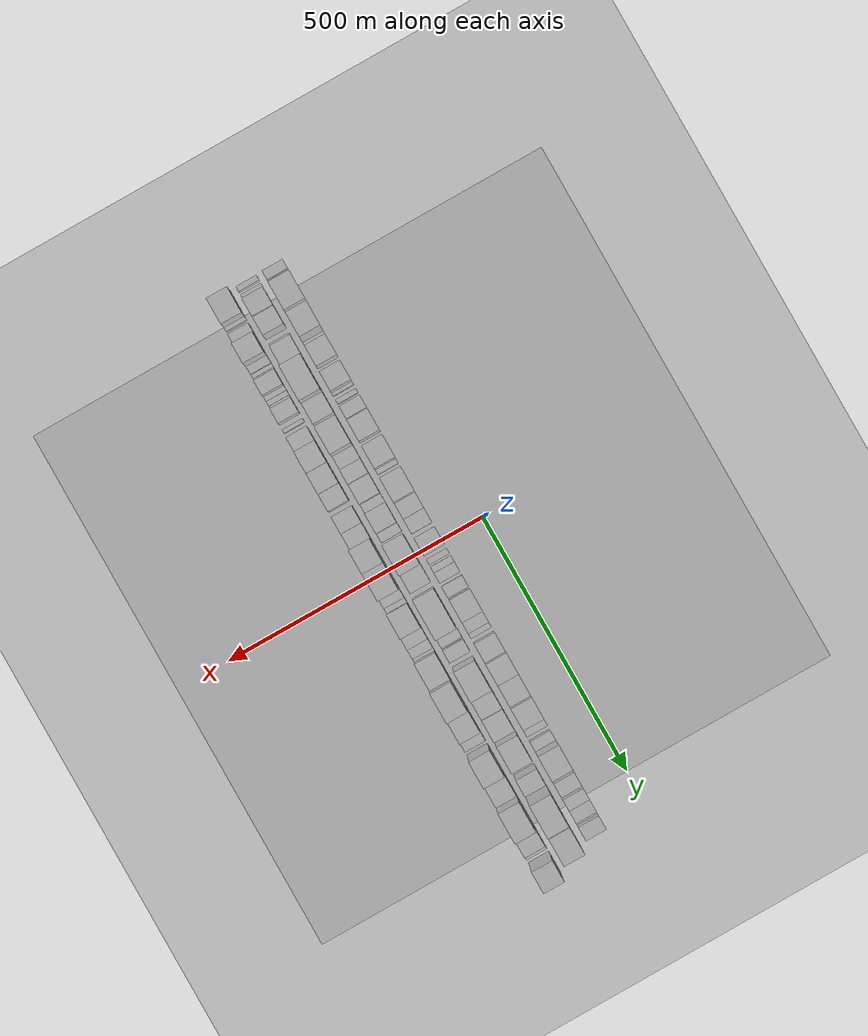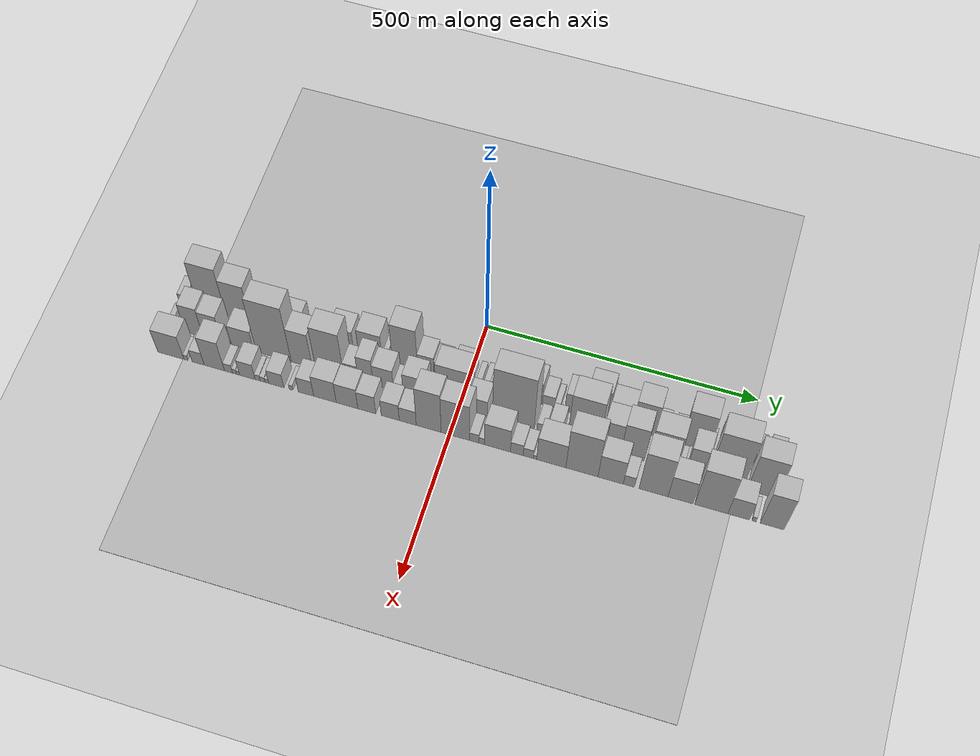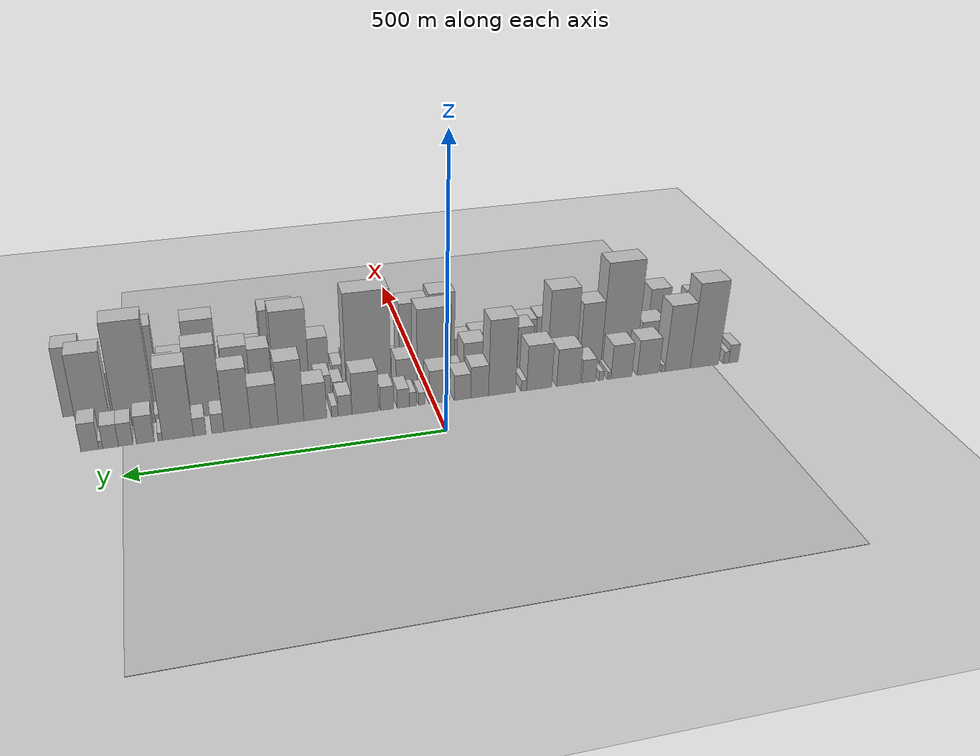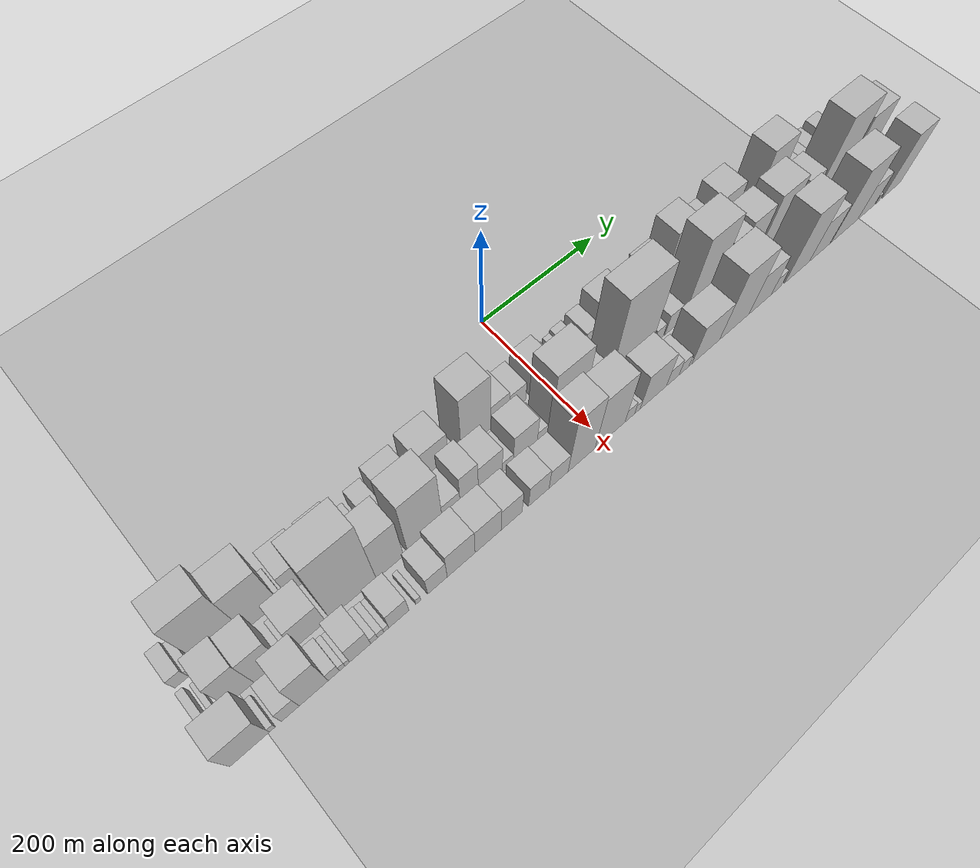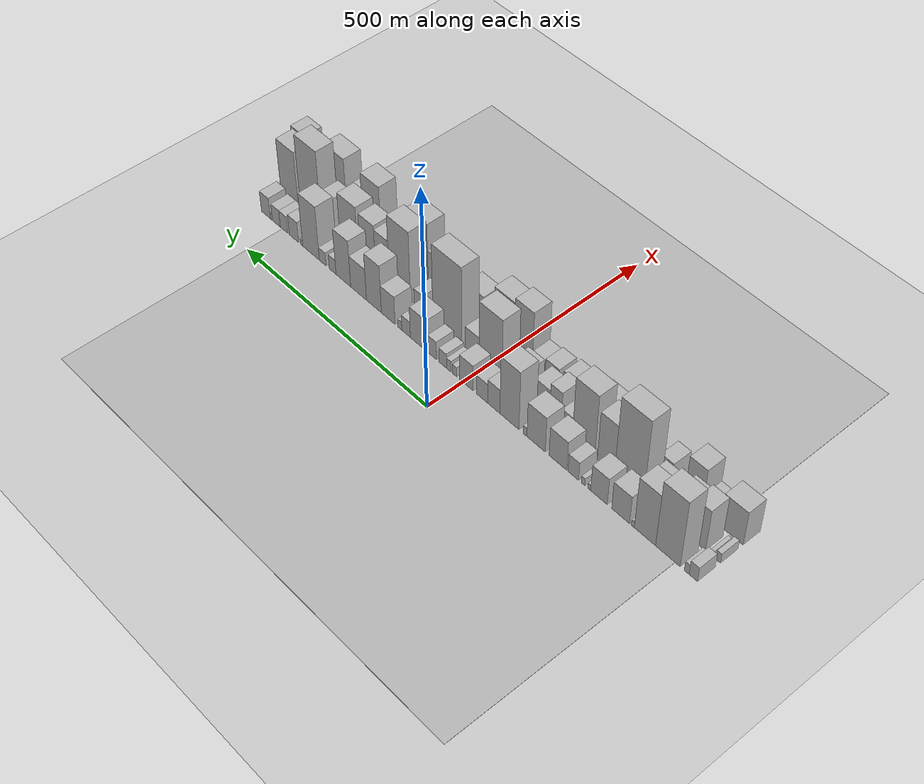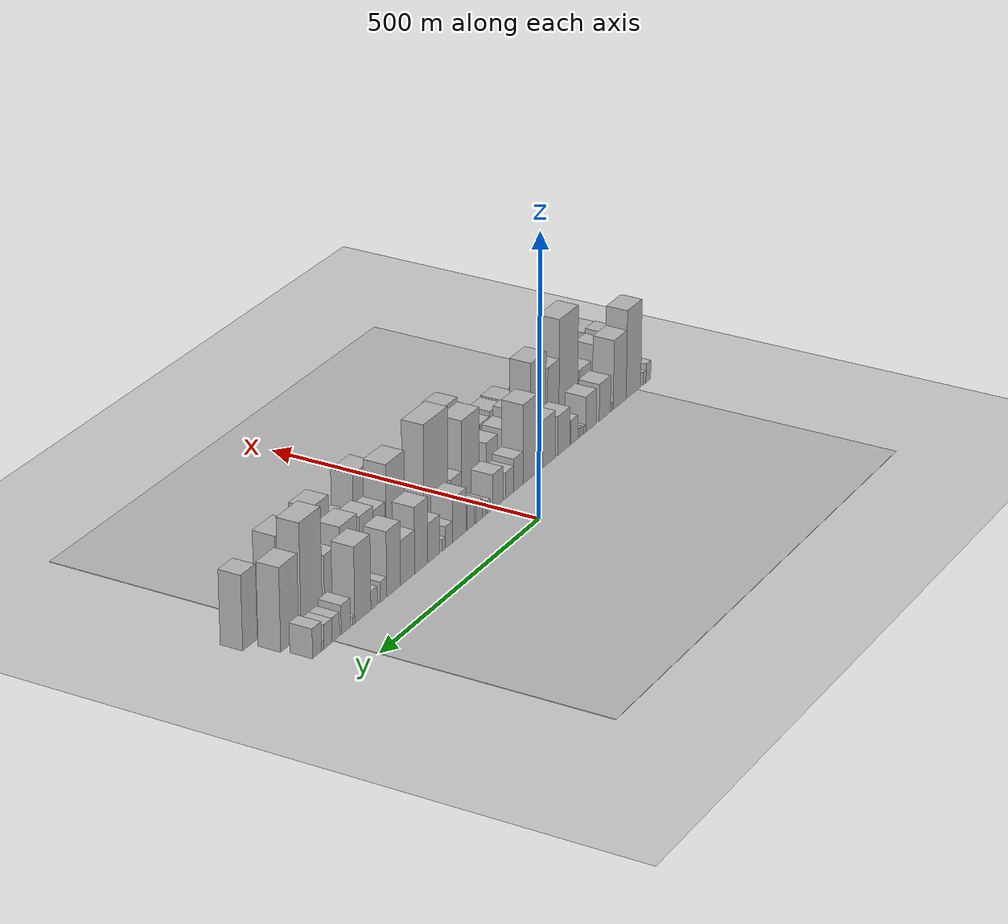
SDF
<?xml version="1.0" encoding="utf-8"?>

<sdf version="1.6">

   <world name="default">

      <gui fullscreen="0">

         <camera name="user_camera">

            <pose>-15 0 4.57585 0 0 0</pose>

            <view_controller>orbit</view_controller>

         </camera>

      </gui>

      <scene>

         <sky>

           <clouds>

             <speed>12</speed>

           </clouds>

         </sky>

         <ambient>0.4 0.4 0.4 1</ambient>

         <background>0.7 0.7 0.7 1</background>

         <shadows>1</shadows>

      </scene>

      <gravity>0 0 -9.8066</gravity>

      <magnetic_field>6e-06 2.3e-05 -4.2e-05</magnetic_field>

      <physics default="0" name="default_physics" type="ode">

         <ode>

            <solver>

               <type>quick</type>

               <iters>10</iters>

               <sor>1.0</sor>

               <use_dynamic_moi_rescaling>0</use_dynamic_moi_rescaling>

            </solver>

            <constraints>

               <cfm>0</cfm>

               <erp>0.2</erp>

               <contact_max_correcting_vel>100</contact_max_correcting_vel>

               <contact_surface_layer>0.001</contact_surface_layer>

            </constraints>

         </ode>

         <max_step_size>0.004</max_step_size>

         <real_time_factor>1</real_time_factor>

         <real_time_update_rate>250</real_time_update_rate>

      </physics>

      <light name="sun" type="directional">

         <cast_shadows>1</cast_shadows>

         <pose>0 0 10 0 0 0</pose>

         <diffuse>0.8 0.8 0.8 1</diffuse>

         <specular>0.2 0.2 0.2 1</specular>

         <attenuation>

            <range>1000</range>

            <constant>0.9</constant>

            <linear>0.01</linear>

            <quadratic>0.001</quadratic>

         </attenuation>

         <direction>-0.5 0.1 -0.9</direction>

      </light>

      <include>

         <name>ground_plane_1</name>

         <uri>model://HANNAS_ground_plane</uri>

         <pose>0 0 0  0 0 0</pose>

      </include>

      <include>

         <name>ground_plane_2</name>

         <uri>model://HANNAS_ground_plane</uri>

         <pose>100 0 0  0 0 0</pose>

      </include>

      <model name="building_1">

         <static>1</static>

         <pose frame="">100.0000 -538.9919 0 0.000000 0.000000 0.000000</pose>

         <link name="link">

            <pose frame="">0 0 18.00 0 0 0</pose>

            <collision name="collision">

               <geometry>

                  <box>

                     <size>40.0000 18.0163 36.0000</size>

                  </box>

               </geometry>

               <max_contacts>10</max_contacts>

               <surface>

                  <contact>

                     <ode/>

                  </contact>

                  <bounce/>

                  <friction>

                     <torsional>

                        <ode/>

                     </torsional>

                     <ode/>

                  </friction>

               </surface>

            </collision>

            <visual name="visual">

               <cast_shadows>0</cast_shadows>

               <geometry>

                  <box>

                     <size>40.0000 18.0163 36.0000</size>

                  </box>

               </geometry>

               <material>

                  <script>

                     <uri>model://HANNAS_wall/materials/scripts</uri>

                     <uri>model://HANNAS_wall/materials/textures</uri>

                     <name>vrc/HANNAS_wall</name>

                  </script>

               </material>

            </visual>

            <self_collide>0</self_collide>

            <enable_wind>0</enable_wind>

            <kinematic>0</kinematic>

         </link>

      </model>

      <model name="building_2">

         <static>1</static>

         <pose frame="">100.0000 -524.8373 0 0.000000 0.000000 0.000000</pose>

         <link name="link">

            <pose frame="">0 0 12.00 0 0 0</pose>

            <collision name="collision">

               <geometry>

                  <box>

                     <size>40.0000 10.2929 24.0000</size>

                  </box>

               </geometry>

               <max_contacts>10</max_contacts>

               <surface>

                  <contact>

                     <ode/>

                  </contact>

                  <bounce/>

                  <friction>

                     <torsional>

                        <ode/>

                     </torsional>

                     <ode/>

                  </friction>

               </surface>

            </collision>

            <visual name="visual">

               <cast_shadows>0</cast_shadows>

               <geometry>

                  <box>

                     <size>40.0000 10.2929 24.0000</size>

                  </box>

               </geometry>

               <material>

                  <script>

                     <uri>model://HANNAS_wall/materials/scripts</uri>

                     <uri>model://HANNAS_wall/materials/textures</uri>

                     <name>vrc/HANNAS_wall</name>

                  </script>

               </material>

            </visual>

            <self_collide>0</self_collide>

            <enable_wind>0</enable_wind>

            <kinematic>0</kinematic>

         </link>

      </model>

      <model name="building_3">

         <static>1</static>

         <pose frame="">100.0000 -483.8453 0 0.000000 0.000000 0.000000</pose>

         <link name="link">

            <pose frame="">0 0 82.50 0 0 0</pose>

            <collision name="collision">

               <geometry>

                  <box>

                     <size>40.0000 53.6910 165.0000</size>

                  </box>

               </geometry>

               <max_contacts>10</max_contacts>

               <surface>

                  <contact>

                     <ode/>

                  </contact>

                  <bounce/>

                  <friction>

                     <torsional>

                        <ode/>

                     </torsional>

                     <ode/>

                  </friction>

               </surface>

            </collision>

            <visual name="visual">

               <cast_shadows>0</cast_shadows>

               <geometry>

                  <box>

                     <size>40.0000 53.6910 165.0000</size>

                  </box>

               </geometry>

               <material>

                  <script>

                     <uri>model://HANNAS_wall/materials/scripts</uri>

                     <uri>model://HANNAS_wall/materials/textures</uri>

                     <name>vrc/HANNAS_wall</name>

                  </script>

               </material>

            </visual>

            <self_collide>0</self_collide>

            <enable_wind>0</enable_wind>

            <kinematic>0</kinematic>

         </link>

      </model>

      <model name="building_4">

         <static>1</static>

         <pose frame="">100.0000 -433.3912 0 0.000000 0.000000 0.000000</pose>

         <link name="link">

            <pose frame="">0 0 64.50 0 0 0</pose>

            <collision name="collision">

               <geometry>

                  <box>

                     <size>40.0000 47.2173 129.0000</size>

                  </box>

               </geometry>

               <max_contacts>10</max_contacts>

               <surface>

                  <contact>

                     <ode/>

                  </contact>

                  <bounce/>

                  <friction>

                     <torsional>

                        <ode/>

                     </torsional>

                     <ode/>

                  </friction>

               </surface>

            </collision>

            <visual name="visual">

               <cast_shadows>0</cast_shadows>

               <geometry>

                  <box>

                     <size>40.0000 47.2173 129.0000</size>

                  </box>

               </geometry>

               <material>

                  <script>

                     <uri>model://HANNAS_wall/materials/scripts</uri>

                     <uri>model://HANNAS_wall/materials/textures</uri>

                     <name>vrc/HANNAS_wall</name>

                  </script>

               </material>

            </visual>

            <self_collide>0</self_collide>

            <enable_wind>0</enable_wind>

            <kinematic>0</kinematic>

         </link>

      </model>

      <model name="building_5">

         <static>1</static>

         <pose frame="">100.0000 -406.5223 0 0.000000 0.000000 0.000000</pose>

         <link name="link">

            <pose frame="">0 0 7.50 0 0 0</pose>

            <collision name="collision">

               <geometry>

                  <box>

                     <size>40.0000 6.5204 15.0000</size>

                  </box>

               </geometry>

               <max_contacts>10</max_contacts>

               <surface>

                  <contact>

                     <ode/>

                  </contact>

                  <bounce/>

                  <friction>

                     <torsional>

                        <ode/>

                     </torsional>

                     <ode/>

                  </friction>

               </surface>

            </collision>

            <visual name="visual">

               <cast_shadows>0</cast_shadows>

               <geometry>

                  <box>

                     <size>40.0000 6.5204 15.0000</size>

                  </box>

               </geometry>

               <material>

                  <script>

                     <uri>model://HANNAS_wall/materials/scripts</uri>

                     <uri>model://HANNAS_wall/materials/textures</uri>

                     <name>vrc/HANNAS_wall</name>

                  </script>

               </material>

            </visual>

            <self_collide>0</self_collide>

            <enable_wind>0</enable_wind>

            <kinematic>0</kinematic>

         </link>

      </model>

      <model name="building_6">

         <static>1</static>

         <pose frame="">100.0000 -379.0470 0 0.000000 0.000000 0.000000</pose>

         <link name="link">

            <pose frame="">0 0 34.50 0 0 0</pose>

            <collision name="collision">

               <geometry>

                  <box>

                     <size>40.0000 40.4301 69.0000</size>

                  </box>

               </geometry>

               <max_contacts>10</max_contacts>

               <surface>

                  <contact>

                     <ode/>

                  </contact>

                  <bounce/>

                  <friction>

                     <torsional>

                        <ode/>

                     </torsional>

                     <ode/>

                  </friction>

               </surface>

            </collision>

            <visual name="visual">

               <cast_shadows>0</cast_shadows>

               <geometry>

                  <box>

                     <size>40.0000 40.4301 69.0000</size>

                  </box>

               </geometry>

               <material>

                  <script>

                     <uri>model://HANNAS_wall/materials/scripts</uri>

                     <uri>model://HANNAS_wall/materials/textures</uri>

                     <name>vrc/HANNAS_wall</name>

                  </script>

               </material>

            </visual>

            <self_collide>0</self_collide>

            <enable_wind>0</enable_wind>

            <kinematic>0</kinematic>

         </link>

      </model>

      <model name="building_7">

         <static>1</static>

         <pose frame="">100.0000 -329.8130 0 0.000000 0.000000 0.000000</pose>

         <link name="link">

            <pose frame="">0 0 33.00 0 0 0</pose>

            <collision name="collision">

               <geometry>

                  <box>

                     <size>40.0000 38.0380 66.0000</size>

                  </box>

               </geometry>

               <max_contacts>10</max_contacts>

               <surface>

                  <contact>

                     <ode/>

                  </contact>

                  <bounce/>

                  <friction>

                     <torsional>

                        <ode/>

                     </torsional>

                     <ode/>

                  </friction>

               </surface>

            </collision>

            <visual name="visual">

               <cast_shadows>0</cast_shadows>

               <geometry>

                  <box>

                     <size>40.0000 38.0380 66.0000</size>

                  </box>

               </geometry>

               <material>

                  <script>

                     <uri>model://HANNAS_wall/materials/scripts</uri>

                     <uri>model://HANNAS_wall/materials/textures</uri>

                     <name>vrc/HANNAS_wall</name>

                  </script>

               </material>

            </visual>

            <self_collide>0</self_collide>

            <enable_wind>0</enable_wind>

            <kinematic>0</kinematic>

         </link>

      </model>

      <model name="building_8">

         <static>1</static>

         <pose frame="">100.0000 -307.6681 0 0.000000 0.000000 0.000000</pose>

         <link name="link">

            <pose frame="">0 0 7.50 0 0 0</pose>

            <collision name="collision">

               <geometry>

                  <box>

                     <size>40.0000 6.2518 15.0000</size>

                  </box>

               </geometry>

               <max_contacts>10</max_contacts>

               <surface>

                  <contact>

                     <ode/>

                  </contact>

                  <bounce/>

                  <friction>

                     <torsional>

                        <ode/>

                     </torsional>

                     <ode/>

                  </friction>

               </surface>

            </collision>

            <visual name="visual">

               <cast_shadows>0</cast_shadows>

               <geometry>

                  <box>

                     <size>40.0000 6.2518 15.0000</size>

                  </box>

               </geometry>

               <material>

                  <script>

                     <uri>model://HANNAS_wall/materials/scripts</uri>

                     <uri>model://HANNAS_wall/materials/textures</uri>

                     <name>vrc/HANNAS_wall</name>

                  </script>

               </material>

            </visual>

            <self_collide>0</self_collide>

            <enable_wind>0</enable_wind>

            <kinematic>0</kinematic>

         </link>

      </model>

      <model name="building_9">

         <static>1</static>

         <pose frame="">100.0000 -293.1980 0 0.000000 0.000000 0.000000</pose>

         <link name="link">

            <pose frame="">0 0 9.00 0 0 0</pose>

            <collision name="collision">

               <geometry>

                  <box>

                     <size>40.0000 8.6883 18.0000</size>

                  </box>

               </geometry>

               <max_contacts>10</max_contacts>

               <surface>

                  <contact>

                     <ode/>

                  </contact>

                  <bounce/>

                  <friction>

                     <torsional>

                        <ode/>

                     </torsional>

                     <ode/>

                  </friction>

               </surface>

            </collision>

            <visual name="visual">

               <cast_shadows>0</cast_shadows>

               <geometry>

                  <box>

                     <size>40.0000 8.6883 18.0000</size>

                  </box>

               </geometry>

               <material>

                  <script>

                     <uri>model://HANNAS_wall/materials/scripts</uri>

                     <uri>model://HANNAS_wall/materials/textures</uri>

                     <name>vrc/HANNAS_wall</name>

                  </script>

               </material>

            </visual>

            <self_collide>0</self_collide>

            <enable_wind>0</enable_wind>

            <kinematic>0</kinematic>

         </link>

      </model>

      <model name="building_10">

         <static>1</static>

         <pose frame="">100.0000 -270.4324 0 0.000000 0.000000 0.000000</pose>

         <link name="link">

            <pose frame="">0 0 22.50 0 0 0</pose>

            <collision name="collision">

               <geometry>

                  <box>

                     <size>40.0000 24.8430 45.0000</size>

                  </box>

               </geometry>

               <max_contacts>10</max_contacts>

               <surface>

                  <contact>

                     <ode/>

                  </contact>

                  <bounce/>

                  <friction>

                     <torsional>

                        <ode/>

                     </torsional>

                     <ode/>

                  </friction>

               </surface>

            </collision>

            <visual name="visual">

               <cast_shadows>0</cast_shadows>

               <geometry>

                  <box>

                     <size>40.0000 24.8430 45.0000</size>

                  </box>

               </geometry>

               <material>

                  <script>

                     <uri>model://HANNAS_wall/materials/scripts</uri>

                     <uri>model://HANNAS_wall/materials/textures</uri>

                     <name>vrc/HANNAS_wall</name>

                  </script>

               </material>

            </visual>

            <self_collide>0</self_collide>

            <enable_wind>0</enable_wind>

            <kinematic>0</kinematic>

         </link>

      </model>

      <model name="building_11">

         <static>1</static>

         <pose frame="">100.0000 -234.0322 0 0.000000 0.000000 0.000000</pose>

         <link name="link">

            <pose frame="">0 0 36.00 0 0 0</pose>

            <collision name="collision">

               <geometry>

                  <box>

                     <size>40.0000 41.9573 72.0000</size>

                  </box>

               </geometry>

               <max_contacts>10</max_contacts>

               <surface>

                  <contact>

                     <ode/>

                  </contact>

                  <bounce/>

                  <friction>

                     <torsional>

                        <ode/>

                     </torsional>

                     <ode/>

                  </friction>

               </surface>

            </collision>

            <visual name="visual">

               <cast_shadows>0</cast_shadows>

               <geometry>

                  <box>

                     <size>40.0000 41.9573 72.0000</size>

                  </box>

               </geometry>

               <material>

                  <script>

                     <uri>model://HANNAS_wall/materials/scripts</uri>

                     <uri>model://HANNAS_wall/materials/textures</uri>

                     <name>vrc/HANNAS_wall</name>

                  </script>

               </material>

            </visual>

            <self_collide>0</self_collide>

            <enable_wind>0</enable_wind>

            <kinematic>0</kinematic>

         </link>

      </model>

      <model name="building_12">

         <static>1</static>

         <pose frame="">100.0000 -181.8780 0 0.000000 0.000000 0.000000</pose>

         <link name="link">

            <pose frame="">0 0 43.50 0 0 0</pose>

            <collision name="collision">

               <geometry>

                  <box>

                     <size>40.0000 44.3511 87.0000</size>

                  </box>

               </geometry>

               <max_contacts>10</max_contacts>

               <surface>

                  <contact>

                     <ode/>

                  </contact>

                  <bounce/>

                  <friction>

                     <torsional>

                        <ode/>

                     </torsional>

                     <ode/>

                  </friction>

               </surface>

            </collision>

            <visual name="visual">

               <cast_shadows>0</cast_shadows>

               <geometry>

                  <box>

                     <size>40.0000 44.3511 87.0000</size>

                  </box>

               </geometry>

               <material>

                  <script>

                     <uri>model://HANNAS_wall/materials/scripts</uri>

                     <uri>model://HANNAS_wall/materials/textures</uri>

                     <name>vrc/HANNAS_wall</name>

                  </script>

               </material>

            </visual>

            <self_collide>0</self_collide>

            <enable_wind>0</enable_wind>

            <kinematic>0</kinematic>

         </link>

      </model>

      <model name="building_13">

         <static>1</static>

         <pose frame="">100.0000 -154.9889 0 0.000000 0.000000 0.000000</pose>

         <link name="link">

            <pose frame="">0 0 10.50 0 0 0</pose>

            <collision name="collision">

               <geometry>

                  <box>

                     <size>40.0000 9.4271 21.0000</size>

                  </box>

               </geometry>

               <max_contacts>10</max_contacts>

               <surface>

                  <contact>

                     <ode/>

                  </contact>

                  <bounce/>

                  <friction>

                     <torsional>

                        <ode/>

                     </torsional>

                     <ode/>

                  </friction>

               </surface>

            </collision>

            <visual name="visual">

               <cast_shadows>0</cast_shadows>

               <geometry>

                  <box>

                     <size>40.0000 9.4271 21.0000</size>

                  </box>

               </geometry>

               <material>

                  <script>

                     <uri>model://HANNAS_wall/materials/scripts</uri>

                     <uri>model://HANNAS_wall/materials/textures</uri>

                     <name>vrc/HANNAS_wall</name>

                  </script>

               </material>

            </visual>

            <self_collide>0</self_collide>

            <enable_wind>0</enable_wind>

            <kinematic>0</kinematic>

         </link>

      </model>

      <model name="building_14">

         <static>1</static>

         <pose frame="">100.0000 -116.7056 0 0.000000 0.000000 0.000000</pose>

         <link name="link">

            <pose frame="">0 0 72.00 0 0 0</pose>

            <collision name="collision">

               <geometry>

                  <box>

                     <size>40.0000 47.1394 144.0000</size>

                  </box>

               </geometry>

               <max_contacts>10</max_contacts>

               <surface>

                  <contact>

                     <ode/>

                  </contact>

                  <bounce/>

                  <friction>

                     <torsional>

                        <ode/>

                     </torsional>

                     <ode/>

                  </friction>

               </surface>

            </collision>

            <visual name="visual">

               <cast_shadows>0</cast_shadows>

               <geometry>

                  <box>

                     <size>40.0000 47.1394 144.0000</size>

                  </box>

               </geometry>

               <material>

                  <script>

                     <uri>model://HANNAS_wall/materials/scripts</uri>

                     <uri>model://HANNAS_wall/materials/textures</uri>

                     <name>vrc/HANNAS_wall</name>

                  </script>

               </material>

            </visual>

            <self_collide>0</self_collide>

            <enable_wind>0</enable_wind>

            <kinematic>0</kinematic>

         </link>

      </model>

      <model name="building_15">

         <static>1</static>

         <pose frame="">100.0000 -77.7543 0 0.000000 0.000000 0.000000</pose>

         <link name="link">

            <pose frame="">0 0 30.00 0 0 0</pose>

            <collision name="collision">

               <geometry>

                  <box>

                     <size>40.0000 30.7633 60.0000</size>

                  </box>

               </geometry>

               <max_contacts>10</max_contacts>

               <surface>

                  <contact>

                     <ode/>

                  </contact>

                  <bounce/>

                  <friction>

                     <torsional>

                        <ode/>

                     </torsional>

                     <ode/>

                  </friction>

               </surface>

            </collision>

            <visual name="visual">

               <cast_shadows>0</cast_shadows>

               <geometry>

                  <box>

                     <size>40.0000 30.7633 60.0000</size>

                  </box>

               </geometry>

               <material>

                  <script>

                     <uri>model://HANNAS_wall/materials/scripts</uri>

                     <uri>model://HANNAS_wall/materials/textures</uri>

                     <name>vrc/HANNAS_wall</name>

                  </script>

               </material>

            </visual>

            <self_collide>0</self_collide>

            <enable_wind>0</enable_wind>

            <kinematic>0</kinematic>

         </link>

      </model>

      <model name="building_16">

         <static>1</static>

         <pose frame="">100.0000 -48.2294 0 0.000000 0.000000 0.000000</pose>

         <link name="link">

            <pose frame="">0 0 24.00 0 0 0</pose>

            <collision name="collision">

               <geometry>

                  <box>

                     <size>40.0000 28.2866 48.0000</size>

                  </box>

               </geometry>

               <max_contacts>10</max_contacts>

               <surface>

                  <contact>

                     <ode/>

                  </contact>

                  <bounce/>

                  <friction>

                     <torsional>

                        <ode/>

                     </torsional>

                     <ode/>

                  </friction>

               </surface>

            </collision>

            <visual name="visual">

               <cast_shadows>0</cast_shadows>

               <geometry>

                  <box>

                     <size>40.0000 28.2866 48.0000</size>

                  </box>

               </geometry>

               <material>

                  <script>

                     <uri>model://HANNAS_wall/materials/scripts</uri>

                     <uri>model://HANNAS_wall/materials/textures</uri>

                     <name>vrc/HANNAS_wall</name>

                  </script>

               </material>

            </visual>

            <self_collide>0</self_collide>

            <enable_wind>0</enable_wind>

            <kinematic>0</kinematic>

         </link>

      </model>

      <model name="building_17">

         <static>1</static>

         <pose frame="">100.0000 -8.6948 0 0.000000 0.000000 0.000000</pose>

         <link name="link">

            <pose frame="">0 0 31.50 0 0 0</pose>

            <collision name="collision">

               <geometry>

                  <box>

                     <size>40.0000 34.7825 63.0000</size>

                  </box>

               </geometry>

               <max_contacts>10</max_contacts>

               <surface>

                  <contact>

                     <ode/>

                  </contact>

                  <bounce/>

                  <friction>

                     <torsional>

                        <ode/>

                     </torsional>

                     <ode/>

                  </friction>

               </surface>

            </collision>

            <visual name="visual">

               <cast_shadows>0</cast_shadows>

               <geometry>

                  <box>

                     <size>40.0000 34.7825 63.0000</size>

                  </box>

               </geometry>

               <material>

                  <script>

                     <uri>model://HANNAS_wall/materials/scripts</uri>

                     <uri>model://HANNAS_wall/materials/textures</uri>

                     <name>vrc/HANNAS_wall</name>

                  </script>

               </material>

            </visual>

            <self_collide>0</self_collide>

            <enable_wind>0</enable_wind>

            <kinematic>0</kinematic>

         </link>

      </model>

      <model name="building_18">

         <static>1</static>

         <pose frame="">100.0000 20.9811 0 0.000000 0.000000 0.000000</pose>

         <link name="link">

            <pose frame="">0 0 12.00 0 0 0</pose>

            <collision name="collision">

               <geometry>

                  <box>

                     <size>40.0000 10.5693 24.0000</size>

                  </box>

               </geometry>

               <max_contacts>10</max_contacts>

               <surface>

                  <contact>

                     <ode/>

                  </contact>

                  <bounce/>

                  <friction>

                     <torsional>

                        <ode/>

                     </torsional>

                     <ode/>

                  </friction>

               </surface>

            </collision>

            <visual name="visual">

               <cast_shadows>0</cast_shadows>

               <geometry>

                  <box>

                     <size>40.0000 10.5693 24.0000</size>

                  </box>

               </geometry>

               <material>

                  <script>

                     <uri>model://HANNAS_wall/materials/scripts</uri>

                     <uri>model://HANNAS_wall/materials/textures</uri>

                     <name>vrc/HANNAS_wall</name>

                  </script>

               </material>

            </visual>

            <self_collide>0</self_collide>

            <enable_wind>0</enable_wind>

            <kinematic>0</kinematic>

         </link>

      </model>

      <model name="building_19">

         <static>1</static>

         <pose frame="">100.0000 36.2725 0 0.000000 0.000000 0.000000</pose>

         <link name="link">

            <pose frame="">0 0 13.50 0 0 0</pose>

            <collision name="collision">

               <geometry>

                  <box>

                     <size>40.0000 12.0134 27.0000</size>

                  </box>

               </geometry>

               <max_contacts>10</max_contacts>

               <surface>

                  <contact>

                     <ode/>

                  </contact>

                  <bounce/>

                  <friction>

                     <torsional>

                        <ode/>

                     </torsional>

                     <ode/>

                  </friction>

               </surface>

            </collision>

            <visual name="visual">

               <cast_shadows>0</cast_shadows>

               <geometry>

                  <box>

                     <size>40.0000 12.0134 27.0000</size>

                  </box>

               </geometry>

               <material>

                  <script>

                     <uri>model://HANNAS_wall/materials/scripts</uri>

                     <uri>model://HANNAS_wall/materials/textures</uri>

                     <name>vrc/HANNAS_wall</name>

                  </script>

               </material>

            </visual>

            <self_collide>0</self_collide>

            <enable_wind>0</enable_wind>

            <kinematic>0</kinematic>

         </link>

      </model>

      <model name="building_20">

         <static>1</static>

         <pose frame="">100.0000 52.2547 0 0.000000 0.000000 0.000000</pose>

         <link name="link">

            <pose frame="">0 0 18.00 0 0 0</pose>

            <collision name="collision">

               <geometry>

                  <box>

                     <size>40.0000 19.9511 36.0000</size>

                  </box>

               </geometry>

               <max_contacts>10</max_contacts>

               <surface>

                  <contact>

                     <ode/>

                  </contact>

                  <bounce/>

                  <friction>

                     <torsional>

                        <ode/>

                     </torsional>

                     <ode/>

                  </friction>

               </surface>

            </collision>

            <visual name="visual">

               <cast_shadows>0</cast_shadows>

               <geometry>

                  <box>

                     <size>40.0000 19.9511 36.0000</size>

                  </box>

               </geometry>

               <material>

                  <script>

                     <uri>model://HANNAS_wall/materials/scripts</uri>

                     <uri>model://HANNAS_wall/materials/textures</uri>

                     <name>vrc/HANNAS_wall</name>

                  </script>

               </material>

            </visual>

            <self_collide>0</self_collide>

            <enable_wind>0</enable_wind>

            <kinematic>0</kinematic>

         </link>

      </model>

      <model name="building_21">

         <static>1</static>

         <pose frame="">100.0000 79.4977 0 0.000000 0.000000 0.000000</pose>

         <link name="link">

            <pose frame="">0 0 22.50 0 0 0</pose>

            <collision name="collision">

               <geometry>

                  <box>

                     <size>40.0000 22.5349 45.0000</size>

                  </box>

               </geometry>

               <max_contacts>10</max_contacts>

               <surface>

                  <contact>

                     <ode/>

                  </contact>

                  <bounce/>

                  <friction>

                     <torsional>

                        <ode/>

                     </torsional>

                     <ode/>

                  </friction>

               </surface>

            </collision>

            <visual name="visual">

               <cast_shadows>0</cast_shadows>

               <geometry>

                  <box>

                     <size>40.0000 22.5349 45.0000</size>

                  </box>

               </geometry>

               <material>

                  <script>

                     <uri>model://HANNAS_wall/materials/scripts</uri>

                     <uri>model://HANNAS_wall/materials/textures</uri>

                     <name>vrc/HANNAS_wall</name>

                  </script>

               </material>

            </visual>

            <self_collide>0</self_collide>

            <enable_wind>0</enable_wind>

            <kinematic>0</kinematic>

         </link>

      </model>

      <model name="building_22">

         <static>1</static>

         <pose frame="">100.0000 115.7366 0 0.000000 0.000000 0.000000</pose>

         <link name="link">

            <pose frame="">0 0 39.00 0 0 0</pose>

            <collision name="collision">

               <geometry>

                  <box>

                     <size>40.0000 43.9428 78.0000</size>

                  </box>

               </geometry>

               <max_contacts>10</max_contacts>

               <surface>

                  <contact>

                     <ode/>

                  </contact>

                  <bounce/>

                  <friction>

                     <torsional>

                        <ode/>

                     </torsional>

                     <ode/>

                  </friction>

               </surface>

            </collision>

            <visual name="visual">

               <cast_shadows>0</cast_shadows>

               <geometry>

                  <box>

                     <size>40.0000 43.9428 78.0000</size>

                  </box>

               </geometry>

               <material>

                  <script>

                     <uri>model://HANNAS_wall/materials/scripts</uri>

                     <uri>model://HANNAS_wall/materials/textures</uri>

                     <name>vrc/HANNAS_wall</name>

                  </script>

               </material>

            </visual>

            <self_collide>0</self_collide>

            <enable_wind>0</enable_wind>

            <kinematic>0</kinematic>

         </link>

      </model>

      <model name="building_23">

         <static>1</static>

         <pose frame="">100.0000 149.1312 0 0.000000 0.000000 0.000000</pose>

         <link name="link">

            <pose frame="">0 0 19.50 0 0 0</pose>

            <collision name="collision">

               <geometry>

                  <box>

                     <size>40.0000 22.8464 39.0000</size>

                  </box>

               </geometry>

               <max_contacts>10</max_contacts>

               <surface>

                  <contact>

                     <ode/>

                  </contact>

                  <bounce/>

                  <friction>

                     <torsional>

                        <ode/>

                     </torsional>

                     <ode/>

                  </friction>

               </surface>

            </collision>

            <visual name="visual">

               <cast_shadows>0</cast_shadows>

               <geometry>

                  <box>

                     <size>40.0000 22.8464 39.0000</size>

                  </box>

               </geometry>

               <material>

                  <script>

                     <uri>model://HANNAS_wall/materials/scripts</uri>

                     <uri>model://HANNAS_wall/materials/textures</uri>

                     <name>vrc/HANNAS_wall</name>

                  </script>

               </material>

            </visual>

            <self_collide>0</self_collide>

            <enable_wind>0</enable_wind>

            <kinematic>0</kinematic>

         </link>

      </model>

      <model name="building_24">

         <static>1</static>

         <pose frame="">100.0000 165.6955 0 0.000000 0.000000 0.000000</pose>

         <link name="link">

            <pose frame="">0 0 10.50 0 0 0</pose>

            <collision name="collision">

               <geometry>

                  <box>

                     <size>40.0000 10.2822 21.0000</size>

                  </box>

               </geometry>

               <max_contacts>10</max_contacts>

               <surface>

                  <contact>

                     <ode/>

                  </contact>

                  <bounce/>

                  <friction>

                     <torsional>

                        <ode/>

                     </torsional>

                     <ode/>

                  </friction>

               </surface>

            </collision>

            <visual name="visual">

               <cast_shadows>0</cast_shadows>

               <geometry>

                  <box>

                     <size>40.0000 10.2822 21.0000</size>

                  </box>

               </geometry>

               <material>

                  <script>

                     <uri>model://HANNAS_wall/materials/scripts</uri>

                     <uri>model://HANNAS_wall/materials/textures</uri>

                     <name>vrc/HANNAS_wall</name>

                  </script>

               </material>

            </visual>

            <self_collide>0</self_collide>

            <enable_wind>0</enable_wind>

            <kinematic>0</kinematic>

         </link>

      </model>

      <model name="building_25">

         <static>1</static>

         <pose frame="">100.0000 197.4413 0 0.000000 0.000000 0.000000</pose>

         <link name="link">

            <pose frame="">0 0 34.50 0 0 0</pose>

            <collision name="collision">

               <geometry>

                  <box>

                     <size>40.0000 37.2094 69.0000</size>

                  </box>

               </geometry>

               <max_contacts>10</max_contacts>

               <surface>

                  <contact>

                     <ode/>

                  </contact>

                  <bounce/>

                  <friction>

                     <torsional>

                        <ode/>

                     </torsional>

                     <ode/>

                  </friction>

               </surface>

            </collision>

            <visual name="visual">

               <cast_shadows>0</cast_shadows>

               <geometry>

                  <box>

                     <size>40.0000 37.2094 69.0000</size>

                  </box>

               </geometry>

               <material>

                  <script>

                     <uri>model://HANNAS_wall/materials/scripts</uri>

                     <uri>model://HANNAS_wall/materials/textures</uri>

                     <name>vrc/HANNAS_wall</name>

                  </script>

               </material>

            </visual>

            <self_collide>0</self_collide>

            <enable_wind>0</enable_wind>

            <kinematic>0</kinematic>

         </link>

      </model>

      <model name="building_26">

         <static>1</static>

         <pose frame="">100.0000 236.7408 0 0.000000 0.000000 0.000000</pose>

         <link name="link">

            <pose frame="">0 0 58.50 0 0 0</pose>

            <collision name="collision">

               <geometry>

                  <box>

                     <size>40.0000 41.3896 117.0000</size>

                  </box>

               </geometry>

               <max_contacts>10</max_contacts>

               <surface>

                  <contact>

                     <ode/>

                  </contact>

                  <bounce/>

                  <friction>

                     <torsional>

                        <ode/>

                     </torsional>

                     <ode/>

                  </friction>

               </surface>

            </collision>

            <visual name="visual">

               <cast_shadows>0</cast_shadows>

               <geometry>

                  <box>

                     <size>40.0000 41.3896 117.0000</size>

                  </box>

               </geometry>

               <material>

                  <script>

                     <uri>model://HANNAS_wall/materials/scripts</uri>

                     <uri>model://HANNAS_wall/materials/textures</uri>

                     <name>vrc/HANNAS_wall</name>

                  </script>

               </material>

            </visual>

            <self_collide>0</self_collide>

            <enable_wind>0</enable_wind>

            <kinematic>0</kinematic>

         </link>

      </model>

      <model name="building_27">

         <static>1</static>

         <pose frame="">100.0000 279.3616 0 0.000000 0.000000 0.000000</pose>

         <link name="link">

            <pose frame="">0 0 39.00 0 0 0</pose>

            <collision name="collision">

               <geometry>

                  <box>

                     <size>40.0000 43.8519 78.0000</size>

                  </box>

               </geometry>

               <max_contacts>10</max_contacts>

               <surface>

                  <contact>

                     <ode/>

                  </contact>

                  <bounce/>

                  <friction>

                     <torsional>

                        <ode/>

                     </torsional>

                     <ode/>

                  </friction>

               </surface>

            </collision>

            <visual name="visual">

               <cast_shadows>0</cast_shadows>

               <geometry>

                  <box>

                     <size>40.0000 43.8519 78.0000</size>

                  </box>

               </geometry>

               <material>

                  <script>

                     <uri>model://HANNAS_wall/materials/scripts</uri>

                     <uri>model://HANNAS_wall/materials/textures</uri>

                     <name>vrc/HANNAS_wall</name>

                  </script>

               </material>

            </visual>

            <self_collide>0</self_collide>

            <enable_wind>0</enable_wind>

            <kinematic>0</kinematic>

         </link>

      </model>

      <model name="building_28">

         <static>1</static>

         <pose frame="">100.0000 322.2497 0 0.000000 0.000000 0.000000</pose>

         <link name="link">

            <pose frame="">0 0 57.00 0 0 0</pose>

            <collision name="collision">

               <geometry>

                  <box>

                     <size>40.0000 41.9244 114.0000</size>

                  </box>

               </geometry>

               <max_contacts>10</max_contacts>

               <surface>

                  <contact>

                     <ode/>

                  </contact>

                  <bounce/>

                  <friction>

                     <torsional>

                        <ode/>

                     </torsional>

                     <ode/>

                  </friction>

               </surface>

            </collision>

            <visual name="visual">

               <cast_shadows>0</cast_shadows>

               <geometry>

                  <box>

                     <size>40.0000 41.9244 114.0000</size>

                  </box>

               </geometry>

               <material>

                  <script>

                     <uri>model://HANNAS_wall/materials/scripts</uri>

                     <uri>model://HANNAS_wall/materials/textures</uri>

                     <name>vrc/HANNAS_wall</name>

                  </script>

               </material>

            </visual>

            <self_collide>0</self_collide>

            <enable_wind>0</enable_wind>

            <kinematic>0</kinematic>

         </link>

      </model>

      <model name="building_29">

         <static>1</static>

         <pose frame="">100.0000 352.7998 0 0.000000 0.000000 0.000000</pose>

         <link name="link">

            <pose frame="">0 0 18.00 0 0 0</pose>

            <collision name="collision">

               <geometry>

                  <box>

                     <size>40.0000 19.1758 36.0000</size>

                  </box>

               </geometry>

               <max_contacts>10</max_contacts>

               <surface>

                  <contact>

                     <ode/>

                  </contact>

                  <bounce/>

                  <friction>

                     <torsional>

                        <ode/>

                     </torsional>

                     <ode/>

                  </friction>

               </surface>

            </collision>

            <visual name="visual">

               <cast_shadows>0</cast_shadows>

               <geometry>

                  <box>

                     <size>40.0000 19.1758 36.0000</size>

                  </box>

               </geometry>

               <material>

                  <script>

                     <uri>model://HANNAS_wall/materials/scripts</uri>

                     <uri>model://HANNAS_wall/materials/textures</uri>

                     <name>vrc/HANNAS_wall</name>

                  </script>

               </material>

            </visual>

            <self_collide>0</self_collide>

            <enable_wind>0</enable_wind>

            <kinematic>0</kinematic>

         </link>

      </model>

      <model name="building_30">

         <static>1</static>

         <pose frame="">100.0000 381.1690 0 0.000000 0.000000 0.000000</pose>

         <link name="link">

            <pose frame="">0 0 16.50 0 0 0</pose>

            <collision name="collision">

               <geometry>

                  <box>

                     <size>40.0000 19.5627 33.0000</size>

                  </box>

               </geometry>

               <max_contacts>10</max_contacts>

               <surface>

                  <contact>

                     <ode/>

                  </contact>

                  <bounce/>

                  <friction>

                     <torsional>

                        <ode/>

                     </torsional>

                     <ode/>

                  </friction>

               </surface>

            </collision>

            <visual name="visual">

               <cast_shadows>0</cast_shadows>

               <geometry>

                  <box>

                     <size>40.0000 19.5627 33.0000</size>

                  </box>

               </geometry>

               <material>

                  <script>

                     <uri>model://HANNAS_wall/materials/scripts</uri>

                     <uri>model://HANNAS_wall/materials/textures</uri>

                     <name>vrc/HANNAS_wall</name>

                  </script>

               </material>

            </visual>

            <self_collide>0</self_collide>

            <enable_wind>0</enable_wind>

            <kinematic>0</kinematic>

         </link>

      </model>

      <model name="building_31">

         <static>1</static>

         <pose frame="">100.0000 415.0121 0 0.000000 0.000000 0.000000</pose>

         <link name="link">

            <pose frame="">0 0 66.00 0 0 0</pose>

            <collision name="collision">

               <geometry>

                  <box>

                     <size>40.0000 48.1235 132.0000</size>

                  </box>

               </geometry>

               <max_contacts>10</max_contacts>

               <surface>

                  <contact>

                     <ode/>

                  </contact>

                  <bounce/>

                  <friction>

                     <torsional>

                        <ode/>

                     </torsional>

                     <ode/>

                  </friction>

               </surface>

            </collision>

            <visual name="visual">

               <cast_shadows>0</cast_shadows>

               <geometry>

                  <box>

                     <size>40.0000 48.1235 132.0000</size>

                  </box>

               </geometry>

               <material>

                  <script>

                     <uri>model://HANNAS_wall/materials/scripts</uri>

                     <uri>model://HANNAS_wall/materials/textures</uri>

                     <name>vrc/HANNAS_wall</name>

                  </script>

               </material>

            </visual>

            <self_collide>0</self_collide>

            <enable_wind>0</enable_wind>

            <kinematic>0</kinematic>

         </link>

      </model>

      <model name="building_32">

         <static>1</static>

         <pose frame="">100.0000 442.3995 0 0.000000 0.000000 0.000000</pose>

         <link name="link">

            <pose frame="">0 0 7.50 0 0 0</pose>

            <collision name="collision">

               <geometry>

                  <box>

                     <size>40.0000 6.6512 15.0000</size>

                  </box>

               </geometry>

               <max_contacts>10</max_contacts>

               <surface>

                  <contact>

                     <ode/>

                  </contact>

                  <bounce/>

                  <friction>

                     <torsional>

                        <ode/>

                     </torsional>

                     <ode/>

                  </friction>

               </surface>

            </collision>

            <visual name="visual">

               <cast_shadows>0</cast_shadows>

               <geometry>

                  <box>

                     <size>40.0000 6.6512 15.0000</size>

                  </box>

               </geometry>

               <material>

                  <script>

                     <uri>model://HANNAS_wall/materials/scripts</uri>

                     <uri>model://HANNAS_wall/materials/textures</uri>

                     <name>vrc/HANNAS_wall</name>

                  </script>

               </material>

            </visual>

            <self_collide>0</self_collide>

            <enable_wind>0</enable_wind>

            <kinematic>0</kinematic>

         </link>

      </model>

      <model name="building_33">

         <static>1</static>

         <pose frame="">100.0000 465.3273 0 0.000000 0.000000 0.000000</pose>

         <link name="link">

            <pose frame="">0 0 25.50 0 0 0</pose>

            <collision name="collision">

               <geometry>

                  <box>

                     <size>40.0000 27.2045 51.0000</size>

                  </box>

               </geometry>

               <max_contacts>10</max_contacts>

               <surface>

                  <contact>

                     <ode/>

                  </contact>

                  <bounce/>

                  <friction>

                     <torsional>

                        <ode/>

                     </torsional>

                     <ode/>

                  </friction>

               </surface>

            </collision>

            <visual name="visual">

               <cast_shadows>0</cast_shadows>

               <geometry>

                  <box>

                     <size>40.0000 27.2045 51.0000</size>

                  </box>

               </geometry>

               <material>

                  <script>

                     <uri>model://HANNAS_wall/materials/scripts</uri>

                     <uri>model://HANNAS_wall/materials/textures</uri>

                     <name>vrc/HANNAS_wall</name>

                  </script>

               </material>

            </visual>

            <self_collide>0</self_collide>

            <enable_wind>0</enable_wind>

            <kinematic>0</kinematic>

         </link>

      </model>

      <model name="building_34">

         <static>1</static>

         <pose frame="">100.0000 494.9482 0 0.000000 0.000000 0.000000</pose>

         <link name="link">

            <pose frame="">0 0 21.00 0 0 0</pose>

            <collision name="collision">

               <geometry>

                  <box>

                     <size>40.0000 22.0373 42.0000</size>

                  </box>

               </geometry>

               <max_contacts>10</max_contacts>

               <surface>

                  <contact>

                     <ode/>

                  </contact>

                  <bounce/>

                  <friction>

                     <torsional>

                        <ode/>

                     </torsional>

                     <ode/>

                  </friction>

               </surface>

            </collision>

            <visual name="visual">

               <cast_shadows>0</cast_shadows>

               <geometry>

                  <box>

                     <size>40.0000 22.0373 42.0000</size>

                  </box>

               </geometry>

               <material>

                  <script>

                     <uri>model://HANNAS_wall/materials/scripts</uri>

                     <uri>model://HANNAS_wall/materials/textures</uri>

                     <name>vrc/HANNAS_wall</name>

                  </script>

               </material>

            </visual>

            <self_collide>0</self_collide>

            <enable_wind>0</enable_wind>

            <kinematic>0</kinematic>

         </link>

      </model>

      <model name="building_35">

         <static>1</static>

         <pose frame="">100.0000 517.9257 0 0.000000 0.000000 0.000000</pose>

         <link name="link">

            <pose frame="">0 0 21.00 0 0 0</pose>

            <collision name="collision">

               <geometry>

                  <box>

                     <size>40.0000 23.9178 42.0000</size>

                  </box>

               </geometry>

               <max_contacts>10</max_contacts>

               <surface>

                  <contact>

                     <ode/>

                  </contact>

                  <bounce/>

                  <friction>

                     <torsional>

                        <ode/>

                     </torsional>

                     <ode/>

                  </friction>

               </surface>

            </collision>

            <visual name="visual">

               <cast_shadows>0</cast_shadows>

               <geometry>

                  <box>

                     <size>40.0000 23.9178 42.0000</size>

                  </box>

               </geometry>

               <material>

                  <script>

                     <uri>model://HANNAS_wall/materials/scripts</uri>

                     <uri>model://HANNAS_wall/materials/textures</uri>

                     <name>vrc/HANNAS_wall</name>

                  </script>

               </material>

            </visual>

            <self_collide>0</self_collide>

            <enable_wind>0</enable_wind>

            <kinematic>0</kinematic>

         </link>

      </model>

      <model name="building_36">

         <static>1</static>

         <pose frame="">100.0000 532.9595 0 0.000000 0.000000 0.000000</pose>

         <link name="link">

            <pose frame="">0 0 7.50 0 0 0</pose>

            <collision name="collision">

               <geometry>

                  <box>

                     <size>40.0000 6.1499 15.0000</size>

                  </box>

               </geometry>

               <max_contacts>10</max_contacts>

               <surface>

                  <contact>

                     <ode/>

                  </contact>

                  <bounce/>

                  <friction>

                     <torsional>

                        <ode/>

                     </torsional>

                     <ode/>

                  </friction>

               </surface>

            </collision>

            <visual name="visual">

               <cast_shadows>0</cast_shadows>

               <geometry>

                  <box>

                     <size>40.0000 6.1499 15.0000</size>

                  </box>

               </geometry>

               <material>

                  <script>

                     <uri>model://HANNAS_wall/materials/scripts</uri>

                     <uri>model://HANNAS_wall/materials/textures</uri>

                     <name>vrc/HANNAS_wall</name>

                  </script>

               </material>

            </visual>

            <self_collide>0</self_collide>

            <enable_wind>0</enable_wind>

            <kinematic>0</kinematic>

         </link>

      </model>

      <model name="building_37">

         <static>1</static>

         <pose frame="">100.0000 549.3498 0 0.000000 0.000000 0.000000</pose>

         <link name="link">

            <pose frame="">0 0 25.50 0 0 0</pose>

            <collision name="collision">

               <geometry>

                  <box>

                     <size>40.0000 26.6306 51.0000</size>

                  </box>

               </geometry>

               <max_contacts>10</max_contacts>

               <surface>

                  <contact>

                     <ode/>

                  </contact>

                  <bounce/>

                  <friction>

                     <torsional>

                        <ode/>

                     </torsional>

                     <ode/>

                  </friction>

               </surface>

            </collision>

            <visual name="visual">

               <cast_shadows>0</cast_shadows>

               <geometry>

                  <box>

                     <size>40.0000 26.6306 51.0000</size>

                  </box>

               </geometry>

               <material>

                  <script>

                     <uri>model://HANNAS_wall/materials/scripts</uri>

                     <uri>model://HANNAS_wall/materials/textures</uri>

                     <name>vrc/HANNAS_wall</name>

                  </script>

               </material>

            </visual>

            <self_collide>0</self_collide>

            <enable_wind>0</enable_wind>

            <kinematic>0</kinematic>

         </link>

      </model>

      <model name="building_38">

         <static>1</static>

         <pose frame="">152.0000 -543.0522 0 0.000000 0.000000 0.000000</pose>

         <link name="link">

            <pose frame="">0 0 12.00 0 0 0</pose>

            <collision name="collision">

               <geometry>

                  <box>

                     <size>40.0000 9.8955 24.0000</size>

                  </box>

               </geometry>

               <max_contacts>10</max_contacts>

               <surface>

                  <contact>

                     <ode/>

                  </contact>

                  <bounce/>

                  <friction>

                     <torsional>

                        <ode/>

                     </torsional>

                     <ode/>

                  </friction>

               </surface>

            </collision>

            <visual name="visual">

               <cast_shadows>0</cast_shadows>

               <geometry>

                  <box>

                     <size>40.0000 9.8955 24.0000</size>

                  </box>

               </geometry>

               <material>

                  <script>

                     <uri>model://HANNAS_wall/materials/scripts</uri>

                     <uri>model://HANNAS_wall/materials/textures</uri>

                     <name>vrc/HANNAS_wall</name>

                  </script>

               </material>

            </visual>

            <self_collide>0</self_collide>

            <enable_wind>0</enable_wind>

            <kinematic>0</kinematic>

         </link>

      </model>

      <model name="building_39">

         <static>1</static>

         <pose frame="">152.0000 -529.5200 0 0.000000 0.000000 0.000000</pose>

         <link name="link">

            <pose frame="">0 0 7.50 0 0 0</pose>

            <collision name="collision">

               <geometry>

                  <box>

                     <size>40.0000 7.1690 15.0000</size>

                  </box>

               </geometry>

               <max_contacts>10</max_contacts>

               <surface>

                  <contact>

                     <ode/>

                  </contact>

                  <bounce/>

                  <friction>

                     <torsional>

                        <ode/>

                     </torsional>

                     <ode/>

                  </friction>

               </surface>

            </collision>

            <visual name="visual">

               <cast_shadows>0</cast_shadows>

               <geometry>

                  <box>

                     <size>40.0000 7.1690 15.0000</size>

                  </box>

               </geometry>

               <material>

                  <script>

                     <uri>model://HANNAS_wall/materials/scripts</uri>

                     <uri>model://HANNAS_wall/materials/textures</uri>

                     <name>vrc/HANNAS_wall</name>

                  </script>

               </material>

            </visual>

            <self_collide>0</self_collide>

            <enable_wind>0</enable_wind>

            <kinematic>0</kinematic>

         </link>

      </model>

      <model name="building_40">

         <static>1</static>

         <pose frame="">152.0000 -498.5052 0 0.000000 0.000000 0.000000</pose>

         <link name="link">

            <pose frame="">0 0 51.00 0 0 0</pose>

            <collision name="collision">

               <geometry>

                  <box>

                     <size>40.0000 34.8606 102.0000</size>

                  </box>

               </geometry>

               <max_contacts>10</max_contacts>

               <surface>

                  <contact>

                     <ode/>

                  </contact>

                  <bounce/>

                  <friction>

                     <torsional>

                        <ode/>

                     </torsional>

                     <ode/>

                  </friction>

               </surface>

            </collision>

            <visual name="visual">

               <cast_shadows>0</cast_shadows>

               <geometry>

                  <box>

                     <size>40.0000 34.8606 102.0000</size>

                  </box>

               </geometry>

               <material>

                  <script>

                     <uri>model://HANNAS_wall/materials/scripts</uri>

                     <uri>model://HANNAS_wall/materials/textures</uri>

                     <name>vrc/HANNAS_wall</name>

                  </script>

               </material>

            </visual>

            <self_collide>0</self_collide>

            <enable_wind>0</enable_wind>

            <kinematic>0</kinematic>

         </link>

      </model>

      <model name="building_41">

         <static>1</static>

         <pose frame="">152.0000 -463.4202 0 0.000000 0.000000 0.000000</pose>

         <link name="link">

            <pose frame="">0 0 46.50 0 0 0</pose>

            <collision name="collision">

               <geometry>

                  <box>

                     <size>40.0000 35.3093 93.0000</size>

                  </box>

               </geometry>

               <max_contacts>10</max_contacts>

               <surface>

                  <contact>

                     <ode/>

                  </contact>

                  <bounce/>

                  <friction>

                     <torsional>

                        <ode/>

                     </torsional>

                     <ode/>

                  </friction>

               </surface>

            </collision>

            <visual name="visual">

               <cast_shadows>0</cast_shadows>

               <geometry>

                  <box>

                     <size>40.0000 35.3093 93.0000</size>

                  </box>

               </geometry>

               <material>

                  <script>

                     <uri>model://HANNAS_wall/materials/scripts</uri>

                     <uri>model://HANNAS_wall/materials/textures</uri>

                     <name>vrc/HANNAS_wall</name>

                  </script>

               </material>

            </visual>

            <self_collide>0</self_collide>

            <enable_wind>0</enable_wind>

            <kinematic>0</kinematic>

         </link>

      </model>

      <model name="building_42">

         <static>1</static>

         <pose frame="">152.0000 -431.5094 0 0.000000 0.000000 0.000000</pose>

         <link name="link">

            <pose frame="">0 0 9.00 0 0 0</pose>

            <collision name="collision">

               <geometry>

                  <box>

                     <size>40.0000 8.5124 18.0000</size>

                  </box>

               </geometry>

               <max_contacts>10</max_contacts>

               <surface>

                  <contact>

                     <ode/>

                  </contact>

                  <bounce/>

                  <friction>

                     <torsional>

                        <ode/>

                     </torsional>

                     <ode/>

                  </friction>

               </surface>

            </collision>

            <visual name="visual">

               <cast_shadows>0</cast_shadows>

               <geometry>

                  <box>

                     <size>40.0000 8.5124 18.0000</size>

                  </box>

               </geometry>

               <material>

                  <script>

                     <uri>model://HANNAS_wall/materials/scripts</uri>

                     <uri>model://HANNAS_wall/materials/textures</uri>

                     <name>vrc/HANNAS_wall</name>

                  </script>

               </material>

            </visual>

            <self_collide>0</self_collide>

            <enable_wind>0</enable_wind>

            <kinematic>0</kinematic>

         </link>

      </model>

      <model name="building_43">

         <static>1</static>

         <pose frame="">152.0000 -405.7660 0 0.000000 0.000000 0.000000</pose>

         <link name="link">

            <pose frame="">0 0 36.00 0 0 0</pose>

            <collision name="collision">

               <geometry>

                  <box>

                     <size>40.0000 42.9744 72.0000</size>

                  </box>

               </geometry>

               <max_contacts>10</max_contacts>

               <surface>

                  <contact>

                     <ode/>

                  </contact>

                  <bounce/>

                  <friction>

                     <torsional>

                        <ode/>

                     </torsional>

                     <ode/>

                  </friction>

               </surface>

            </collision>

            <visual name="visual">

               <cast_shadows>0</cast_shadows>

               <geometry>

                  <box>

                     <size>40.0000 42.9744 72.0000</size>

                  </box>

               </geometry>

               <material>

                  <script>

                     <uri>model://HANNAS_wall/materials/scripts</uri>

                     <uri>model://HANNAS_wall/materials/textures</uri>

                     <name>vrc/HANNAS_wall</name>

                  </script>

               </material>

            </visual>

            <self_collide>0</self_collide>

            <enable_wind>0</enable_wind>

            <kinematic>0</kinematic>

         </link>

      </model>

      <model name="building_44">

         <static>1</static>

         <pose frame="">152.0000 -346.0198 0 0.000000 0.000000 0.000000</pose>

         <link name="link">

            <pose frame="">0 0 97.50 0 0 0</pose>

            <collision name="collision">

               <geometry>

                  <box>

                     <size>40.0000 66.5181 195.0000</size>

                  </box>

               </geometry>

               <max_contacts>10</max_contacts>

               <surface>

                  <contact>

                     <ode/>

                  </contact>

                  <bounce/>

                  <friction>

                     <torsional>

                        <ode/>

                     </torsional>

                     <ode/>

                  </friction>

               </surface>

            </collision>

            <visual name="visual">

               <cast_shadows>0</cast_shadows>

               <geometry>

                  <box>

                     <size>40.0000 66.5181 195.0000</size>

                  </box>

               </geometry>

               <material>

                  <script>

                     <uri>model://HANNAS_wall/materials/scripts</uri>

                     <uri>model://HANNAS_wall/materials/textures</uri>

                     <name>vrc/HANNAS_wall</name>

                  </script>

               </material>

            </visual>

            <self_collide>0</self_collide>

            <enable_wind>0</enable_wind>

            <kinematic>0</kinematic>

         </link>

      </model>

      <model name="building_45">

         <static>1</static>

         <pose frame="">152.0000 -292.8285 0 0.000000 0.000000 0.000000</pose>

         <link name="link">

            <pose frame="">0 0 61.50 0 0 0</pose>

            <collision name="collision">

               <geometry>

                  <box>

                     <size>40.0000 39.8645 123.0000</size>

                  </box>

               </geometry>

               <max_contacts>10</max_contacts>

               <surface>

                  <contact>

                     <ode/>

                  </contact>

                  <bounce/>

                  <friction>

                     <torsional>

                        <ode/>

                     </torsional>

                     <ode/>

                  </friction>

               </surface>

            </collision>

            <visual name="visual">

               <cast_shadows>0</cast_shadows>

               <geometry>

                  <box>

                     <size>40.0000 39.8645 123.0000</size>

                  </box>

               </geometry>

               <material>

                  <script>

                     <uri>model://HANNAS_wall/materials/scripts</uri>

                     <uri>model://HANNAS_wall/materials/textures</uri>

                     <name>vrc/HANNAS_wall</name>

                  </script>

               </material>

            </visual>

            <self_collide>0</self_collide>

            <enable_wind>0</enable_wind>

            <kinematic>0</kinematic>

         </link>

      </model>

      <model name="building_46">

         <static>1</static>

         <pose frame="">152.0000 -240.3963 0 0.000000 0.000000 0.000000</pose>

         <link name="link">

            <pose frame="">0 0 78.00 0 0 0</pose>

            <collision name="collision">

               <geometry>

                  <box>

                     <size>40.0000 52.9998 156.0000</size>

                  </box>

               </geometry>

               <max_contacts>10</max_contacts>

               <surface>

                  <contact>

                     <ode/>

                  </contact>

                  <bounce/>

                  <friction>

                     <torsional>

                        <ode/>

                     </torsional>

                     <ode/>

                  </friction>

               </surface>

            </collision>

            <visual name="visual">

               <cast_shadows>0</cast_shadows>

               <geometry>

                  <box>

                     <size>40.0000 52.9998 156.0000</size>

                  </box>

               </geometry>

               <material>

                  <script>

                     <uri>model://HANNAS_wall/materials/scripts</uri>

                     <uri>model://HANNAS_wall/materials/textures</uri>

                     <name>vrc/HANNAS_wall</name>

                  </script>

               </material>

            </visual>

            <self_collide>0</self_collide>

            <enable_wind>0</enable_wind>

            <kinematic>0</kinematic>

         </link>

      </model>

      <model name="building_47">

         <static>1</static>

         <pose frame="">152.0000 -200.2656 0 0.000000 0.000000 0.000000</pose>

         <link name="link">

            <pose frame="">0 0 27.00 0 0 0</pose>

            <collision name="collision">

               <geometry>

                  <box>

                     <size>40.0000 27.2617 54.0000</size>

                  </box>

               </geometry>

               <max_contacts>10</max_contacts>

               <surface>

                  <contact>

                     <ode/>

                  </contact>

                  <bounce/>

                  <friction>

                     <torsional>

                        <ode/>

                     </torsional>

                     <ode/>

                  </friction>

               </surface>

            </collision>

            <visual name="visual">

               <cast_shadows>0</cast_shadows>

               <geometry>

                  <box>

                     <size>40.0000 27.2617 54.0000</size>

                  </box>

               </geometry>

               <material>

                  <script>

                     <uri>model://HANNAS_wall/materials/scripts</uri>

                     <uri>model://HANNAS_wall/materials/textures</uri>

                     <name>vrc/HANNAS_wall</name>

                  </script>

               </material>

            </visual>

            <self_collide>0</self_collide>

            <enable_wind>0</enable_wind>

            <kinematic>0</kinematic>

         </link>

      </model>

      <model name="building_48">

         <static>1</static>

         <pose frame="">152.0000 -172.6165 0 0.000000 0.000000 0.000000</pose>

         <link name="link">

            <pose frame="">0 0 46.50 0 0 0</pose>

            <collision name="collision">

               <geometry>

                  <box>

                     <size>40.0000 28.0365 93.0000</size>

                  </box>

               </geometry>

               <max_contacts>10</max_contacts>

               <surface>

                  <contact>

                     <ode/>

                  </contact>

                  <bounce/>

                  <friction>

                     <torsional>

                        <ode/>

                     </torsional>

                     <ode/>

                  </friction>

               </surface>

            </collision>

            <visual name="visual">

               <cast_shadows>0</cast_shadows>

               <geometry>

                  <box>

                     <size>40.0000 28.0365 93.0000</size>

                  </box>

               </geometry>

               <material>

                  <script>

                     <uri>model://HANNAS_wall/materials/scripts</uri>

                     <uri>model://HANNAS_wall/materials/textures</uri>

                     <name>vrc/HANNAS_wall</name>

                  </script>

               </material>

            </visual>

            <self_collide>0</self_collide>

            <enable_wind>0</enable_wind>

            <kinematic>0</kinematic>

         </link>

      </model>

      <model name="building_49">

         <static>1</static>

         <pose frame="">152.0000 -139.6529 0 0.000000 0.000000 0.000000</pose>

         <link name="link">

            <pose frame="">0 0 37.50 0 0 0</pose>

            <collision name="collision">

               <geometry>

                  <box>

                     <size>40.0000 37.8907 75.0000</size>

                  </box>

               </geometry>

               <max_contacts>10</max_contacts>

               <surface>

                  <contact>

                     <ode/>

                  </contact>

                  <bounce/>

                  <friction>

                     <torsional>

                        <ode/>

                     </torsional>

                     <ode/>

                  </friction>

               </surface>

            </collision>

            <visual name="visual">

               <cast_shadows>0</cast_shadows>

               <geometry>

                  <box>

                     <size>40.0000 37.8907 75.0000</size>

                  </box>

               </geometry>

               <material>

                  <script>

                     <uri>model://HANNAS_wall/materials/scripts</uri>

                     <uri>model://HANNAS_wall/materials/textures</uri>

                     <name>vrc/HANNAS_wall</name>

                  </script>

               </material>

            </visual>

            <self_collide>0</self_collide>

            <enable_wind>0</enable_wind>

            <kinematic>0</kinematic>

         </link>

      </model>

      <model name="building_50">

         <static>1</static>

         <pose frame="">152.0000 -111.7760 0 0.000000 0.000000 0.000000</pose>

         <link name="link">

            <pose frame="">0 0 15.00 0 0 0</pose>

            <collision name="collision">

               <geometry>

                  <box>

                     <size>40.0000 17.8630 30.0000</size>

                  </box>

               </geometry>

               <max_contacts>10</max_contacts>

               <surface>

                  <contact>

                     <ode/>

                  </contact>

                  <bounce/>

                  <friction>

                     <torsional>

                        <ode/>

                     </torsional>

                     <ode/>

                  </friction>

               </surface>

            </collision>

            <visual name="visual">

               <cast_shadows>0</cast_shadows>

               <geometry>

                  <box>

                     <size>40.0000 17.8630 30.0000</size>

                  </box>

               </geometry>

               <material>

                  <script>

                     <uri>model://HANNAS_wall/materials/scripts</uri>

                     <uri>model://HANNAS_wall/materials/textures</uri>

                     <name>vrc/HANNAS_wall</name>

                  </script>

               </material>

            </visual>

            <self_collide>0</self_collide>

            <enable_wind>0</enable_wind>

            <kinematic>0</kinematic>

         </link>

      </model>

      <model name="building_51">

         <static>1</static>

         <pose frame="">152.0000 -83.2439 0 0.000000 0.000000 0.000000</pose>

         <link name="link">

            <pose frame="">0 0 37.50 0 0 0</pose>

            <collision name="collision">

               <geometry>

                  <box>

                     <size>40.0000 39.2013 75.0000</size>

                  </box>

               </geometry>

               <max_contacts>10</max_contacts>

               <surface>

                  <contact>

                     <ode/>

                  </contact>

                  <bounce/>

                  <friction>

                     <torsional>

                        <ode/>

                     </torsional>

                     <ode/>

                  </friction>

               </surface>

            </collision>

            <visual name="visual">

               <cast_shadows>0</cast_shadows>

               <geometry>

                  <box>

                     <size>40.0000 39.2013 75.0000</size>

                  </box>

               </geometry>

               <material>

                  <script>

                     <uri>model://HANNAS_wall/materials/scripts</uri>

                     <uri>model://HANNAS_wall/materials/textures</uri>

                     <name>vrc/HANNAS_wall</name>

                  </script>

               </material>

            </visual>

            <self_collide>0</self_collide>

            <enable_wind>0</enable_wind>

            <kinematic>0</kinematic>

         </link>

      </model>

      <model name="building_52">

         <static>1</static>

         <pose frame="">152.0000 -55.1002 0 0.000000 0.000000 0.000000</pose>

         <link name="link">

            <pose frame="">0 0 15.00 0 0 0</pose>

            <collision name="collision">

               <geometry>

                  <box>

                     <size>40.0000 17.0862 30.0000</size>

                  </box>

               </geometry>

               <max_contacts>10</max_contacts>

               <surface>

                  <contact>

                     <ode/>

                  </contact>

                  <bounce/>

                  <friction>

                     <torsional>

                        <ode/>

                     </torsional>

                     <ode/>

                  </friction>

               </surface>

            </collision>

            <visual name="visual">

               <cast_shadows>0</cast_shadows>

               <geometry>

                  <box>

                     <size>40.0000 17.0862 30.0000</size>

                  </box>

               </geometry>

               <material>

                  <script>

                     <uri>model://HANNAS_wall/materials/scripts</uri>

                     <uri>model://HANNAS_wall/materials/textures</uri>

                     <name>vrc/HANNAS_wall</name>

                  </script>

               </material>

            </visual>

            <self_collide>0</self_collide>

            <enable_wind>0</enable_wind>

            <kinematic>0</kinematic>

         </link>

      </model>

      <model name="building_53">

         <static>1</static>

         <pose frame="">152.0000 -12.3465 0 0.000000 0.000000 0.000000</pose>

         <link name="link">

            <pose frame="">0 0 75.00 0 0 0</pose>

            <collision name="collision">

               <geometry>

                  <box>

                     <size>40.0000 58.4212 150.0000</size>

                  </box>

               </geometry>

               <max_contacts>10</max_contacts>

               <surface>

                  <contact>

                     <ode/>

                  </contact>

                  <bounce/>

                  <friction>

                     <torsional>

                        <ode/>

                     </torsional>

                     <ode/>

                  </friction>

               </surface>

            </collision>

            <visual name="visual">

               <cast_shadows>0</cast_shadows>

               <geometry>

                  <box>

                     <size>40.0000 58.4212 150.0000</size>

                  </box>

               </geometry>

               <material>

                  <script>

                     <uri>model://HANNAS_wall/materials/scripts</uri>

                     <uri>model://HANNAS_wall/materials/textures</uri>

                     <name>vrc/HANNAS_wall</name>

                  </script>

               </material>

            </visual>

            <self_collide>0</self_collide>

            <enable_wind>0</enable_wind>

            <kinematic>0</kinematic>

         </link>

      </model>

      <model name="building_54">

         <static>1</static>

         <pose frame="">152.0000 34.7778 0 0.000000 0.000000 0.000000</pose>

         <link name="link">

            <pose frame="">0 0 30.00 0 0 0</pose>

            <collision name="collision">

               <geometry>

                  <box>

                     <size>40.0000 35.8274 60.0000</size>

                  </box>

               </geometry>

               <max_contacts>10</max_contacts>

               <surface>

                  <contact>

                     <ode/>

                  </contact>

                  <bounce/>

                  <friction>

                     <torsional>

                        <ode/>

                     </torsional>

                     <ode/>

                  </friction>

               </surface>

            </collision>

            <visual name="visual">

               <cast_shadows>0</cast_shadows>

               <geometry>

                  <box>

                     <size>40.0000 35.8274 60.0000</size>

                  </box>

               </geometry>

               <material>

                  <script>

                     <uri>model://HANNAS_wall/materials/scripts</uri>

                     <uri>model://HANNAS_wall/materials/textures</uri>

                     <name>vrc/HANNAS_wall</name>

                  </script>

               </material>

            </visual>

            <self_collide>0</self_collide>

            <enable_wind>0</enable_wind>

            <kinematic>0</kinematic>

         </link>

      </model>

      <model name="building_55">

         <static>1</static>

         <pose frame="">152.0000 99.6434 0 0.000000 0.000000 0.000000</pose>

         <link name="link">

            <pose frame="">0 0 97.50 0 0 0</pose>

            <collision name="collision">

               <geometry>

                  <box>

                     <size>40.0000 75.9037 195.0000</size>

                  </box>

               </geometry>

               <max_contacts>10</max_contacts>

               <surface>

                  <contact>

                     <ode/>

                  </contact>

                  <bounce/>

                  <friction>

                     <torsional>

                        <ode/>

                     </torsional>

                     <ode/>

                  </friction>

               </surface>

            </collision>

            <visual name="visual">

               <cast_shadows>0</cast_shadows>

               <geometry>

                  <box>

                     <size>40.0000 75.9037 195.0000</size>

                  </box>

               </geometry>

               <material>

                  <script>

                     <uri>model://HANNAS_wall/materials/scripts</uri>

                     <uri>model://HANNAS_wall/materials/textures</uri>

                     <name>vrc/HANNAS_wall</name>

                  </script>

               </material>

            </visual>

            <self_collide>0</self_collide>

            <enable_wind>0</enable_wind>

            <kinematic>0</kinematic>

         </link>

      </model>

      <model name="building_56">

         <static>1</static>

         <pose frame="">152.0000 151.2691 0 0.000000 0.000000 0.000000</pose>

         <link name="link">

            <pose frame="">0 0 16.50 0 0 0</pose>

            <collision name="collision">

               <geometry>

                  <box>

                     <size>40.0000 17.3475 33.0000</size>

                  </box>

               </geometry>

               <max_contacts>10</max_contacts>

               <surface>

                  <contact>

                     <ode/>

                  </contact>

                  <bounce/>

                  <friction>

                     <torsional>

                        <ode/>

                     </torsional>

                     <ode/>

                  </friction>

               </surface>

            </collision>

            <visual name="visual">

               <cast_shadows>0</cast_shadows>

               <geometry>

                  <box>

                     <size>40.0000 17.3475 33.0000</size>

                  </box>

               </geometry>

               <material>

                  <script>

                     <uri>model://HANNAS_wall/materials/scripts</uri>

                     <uri>model://HANNAS_wall/materials/textures</uri>

                     <name>vrc/HANNAS_wall</name>

                  </script>

               </material>

            </visual>

            <self_collide>0</self_collide>

            <enable_wind>0</enable_wind>

            <kinematic>0</kinematic>

         </link>

      </model>

      <model name="building_57">

         <static>1</static>

         <pose frame="">152.0000 175.4248 0 0.000000 0.000000 0.000000</pose>

         <link name="link">

            <pose frame="">0 0 24.00 0 0 0</pose>

            <collision name="collision">

               <geometry>

                  <box>

                     <size>40.0000 24.9639 48.0000</size>

                  </box>

               </geometry>

               <max_contacts>10</max_contacts>

               <surface>

                  <contact>

                     <ode/>

                  </contact>

                  <bounce/>

                  <friction>

                     <torsional>

                        <ode/>

                     </torsional>

                     <ode/>

                  </friction>

               </surface>

            </collision>

            <visual name="visual">

               <cast_shadows>0</cast_shadows>

               <geometry>

                  <box>

                     <size>40.0000 24.9639 48.0000</size>

                  </box>

               </geometry>

               <material>

                  <script>

                     <uri>model://HANNAS_wall/materials/scripts</uri>

                     <uri>model://HANNAS_wall/materials/textures</uri>

                     <name>vrc/HANNAS_wall</name>

                  </script>

               </material>

            </visual>

            <self_collide>0</self_collide>

            <enable_wind>0</enable_wind>

            <kinematic>0</kinematic>

         </link>

      </model>

      <model name="building_58">

         <static>1</static>

         <pose frame="">152.0000 226.5765 0 0.000000 0.000000 0.000000</pose>

         <link name="link">

            <pose frame="">0 0 88.50 0 0 0</pose>

            <collision name="collision">

               <geometry>

                  <box>

                     <size>40.0000 57.3395 177.0000</size>

                  </box>

               </geometry>

               <max_contacts>10</max_contacts>

               <surface>

                  <contact>

                     <ode/>

                  </contact>

                  <bounce/>

                  <friction>

                     <torsional>

                        <ode/>

                     </torsional>

                     <ode/>

                  </friction>

               </surface>

            </collision>

            <visual name="visual">

               <cast_shadows>0</cast_shadows>

               <geometry>

                  <box>

                     <size>40.0000 57.3395 177.0000</size>

                  </box>

               </geometry>

               <material>

                  <script>

                     <uri>model://HANNAS_wall/materials/scripts</uri>

                     <uri>model://HANNAS_wall/materials/textures</uri>

                     <name>vrc/HANNAS_wall</name>

                  </script>

               </material>

            </visual>

            <self_collide>0</self_collide>

            <enable_wind>0</enable_wind>

            <kinematic>0</kinematic>

         </link>

      </model>

      <model name="building_59">

         <static>1</static>

         <pose frame="">152.0000 275.9863 0 0.000000 0.000000 0.000000</pose>

         <link name="link">

            <pose frame="">0 0 57.00 0 0 0</pose>

            <collision name="collision">

               <geometry>

                  <box>

                     <size>40.0000 35.4802 114.0000</size>

                  </box>

               </geometry>

               <max_contacts>10</max_contacts>

               <surface>

                  <contact>

                     <ode/>

                  </contact>

                  <bounce/>

                  <friction>

                     <torsional>

                        <ode/>

                     </torsional>

                     <ode/>

                  </friction>

               </surface>

            </collision>

            <visual name="visual">

               <cast_shadows>0</cast_shadows>

               <geometry>

                  <box>

                     <size>40.0000 35.4802 114.0000</size>

                  </box>

               </geometry>

               <material>

                  <script>

                     <uri>model://HANNAS_wall/materials/scripts</uri>

                     <uri>model://HANNAS_wall/materials/textures</uri>

                     <name>vrc/HANNAS_wall</name>

                  </script>

               </material>

            </visual>

            <self_collide>0</self_collide>

            <enable_wind>0</enable_wind>

            <kinematic>0</kinematic>

         </link>

      </model>

      <model name="building_60">

         <static>1</static>

         <pose frame="">152.0000 314.8461 0 0.000000 0.000000 0.000000</pose>

         <link name="link">

            <pose frame="">0 0 61.50 0 0 0</pose>

            <collision name="collision">

               <geometry>

                  <box>

                     <size>40.0000 42.2395 123.0000</size>

                  </box>

               </geometry>

               <max_contacts>10</max_contacts>

               <surface>

                  <contact>

                     <ode/>

                  </contact>

                  <bounce/>

                  <friction>

                     <torsional>

                        <ode/>

                     </torsional>

                     <ode/>

                  </friction>

               </surface>

            </collision>

            <visual name="visual">

               <cast_shadows>0</cast_shadows>

               <geometry>

                  <box>

                     <size>40.0000 42.2395 123.0000</size>

                  </box>

               </geometry>

               <material>

                  <script>

                     <uri>model://HANNAS_wall/materials/scripts</uri>

                     <uri>model://HANNAS_wall/materials/textures</uri>

                     <name>vrc/HANNAS_wall</name>

                  </script>

               </material>

            </visual>

            <self_collide>0</self_collide>

            <enable_wind>0</enable_wind>

            <kinematic>0</kinematic>

         </link>

      </model>

      <model name="building_61">

         <static>1</static>

         <pose frame="">152.0000 368.6090 0 0.000000 0.000000 0.000000</pose>

         <link name="link">

            <pose frame="">0 0 66.00 0 0 0</pose>

            <collision name="collision">

               <geometry>

                  <box>

                     <size>40.0000 51.2863 132.0000</size>

                  </box>

               </geometry>

               <max_contacts>10</max_contacts>

               <surface>

                  <contact>

                     <ode/>

                  </contact>

                  <bounce/>

                  <friction>

                     <torsional>

                        <ode/>

                     </torsional>

                     <ode/>

                  </friction>

               </surface>

            </collision>

            <visual name="visual">

               <cast_shadows>0</cast_shadows>

               <geometry>

                  <box>

                     <size>40.0000 51.2863 132.0000</size>

                  </box>

               </geometry>

               <material>

                  <script>

                     <uri>model://HANNAS_wall/materials/scripts</uri>

                     <uri>model://HANNAS_wall/materials/textures</uri>

                     <name>vrc/HANNAS_wall</name>

                  </script>

               </material>

            </visual>

            <self_collide>0</self_collide>

            <enable_wind>0</enable_wind>

            <kinematic>0</kinematic>

         </link>

      </model>

      <model name="building_62">

         <static>1</static>

         <pose frame="">152.0000 399.4510 0 0.000000 0.000000 0.000000</pose>

         <link name="link">

            <pose frame="">0 0 12.00 0 0 0</pose>

            <collision name="collision">

               <geometry>

                  <box>

                     <size>40.0000 10.3978 24.0000</size>

                  </box>

               </geometry>

               <max_contacts>10</max_contacts>

               <surface>

                  <contact>

                     <ode/>

                  </contact>

                  <bounce/>

                  <friction>

                     <torsional>

                        <ode/>

                     </torsional>

                     <ode/>

                  </friction>

               </surface>

            </collision>

            <visual name="visual">

               <cast_shadows>0</cast_shadows>

               <geometry>

                  <box>

                     <size>40.0000 10.3978 24.0000</size>

                  </box>

               </geometry>

               <material>

                  <script>

                     <uri>model://HANNAS_wall/materials/scripts</uri>

                     <uri>model://HANNAS_wall/materials/textures</uri>

                     <name>vrc/HANNAS_wall</name>

                  </script>

               </material>

            </visual>

            <self_collide>0</self_collide>

            <enable_wind>0</enable_wind>

            <kinematic>0</kinematic>

         </link>

      </model>

      <model name="building_63">

         <static>1</static>

         <pose frame="">152.0000 425.5350 0 0.000000 0.000000 0.000000</pose>

         <link name="link">

            <pose frame="">0 0 52.50 0 0 0</pose>

            <collision name="collision">

               <geometry>

                  <box>

                     <size>40.0000 31.7702 105.0000</size>

                  </box>

               </geometry>

               <max_contacts>10</max_contacts>

               <surface>

                  <contact>

                     <ode/>

                  </contact>

                  <bounce/>

                  <friction>

                     <torsional>

                        <ode/>

                     </torsional>

                     <ode/>

                  </friction>

               </surface>

            </collision>

            <visual name="visual">

               <cast_shadows>0</cast_shadows>

               <geometry>

                  <box>

                     <size>40.0000 31.7702 105.0000</size>

                  </box>

               </geometry>

               <material>

                  <script>

                     <uri>model://HANNAS_wall/materials/scripts</uri>

                     <uri>model://HANNAS_wall/materials/textures</uri>

                     <name>vrc/HANNAS_wall</name>

                  </script>

               </material>

            </visual>

            <self_collide>0</self_collide>

            <enable_wind>0</enable_wind>

            <kinematic>0</kinematic>

         </link>

      </model>

      <model name="building_64">

         <static>1</static>

         <pose frame="">152.0000 444.9514 0 0.000000 0.000000 0.000000</pose>

         <link name="link">

            <pose frame="">0 0 7.50 0 0 0</pose>

            <collision name="collision">

               <geometry>

                  <box>

                     <size>40.0000 7.0624 15.0000</size>

                  </box>

               </geometry>

               <max_contacts>10</max_contacts>

               <surface>

                  <contact>

                     <ode/>

                  </contact>

                  <bounce/>

                  <friction>

                     <torsional>

                        <ode/>

                     </torsional>

                     <ode/>

                  </friction>

               </surface>

            </collision>

            <visual name="visual">

               <cast_shadows>0</cast_shadows>

               <geometry>

                  <box>

                     <size>40.0000 7.0624 15.0000</size>

                  </box>

               </geometry>

               <material>

                  <script>

                     <uri>model://HANNAS_wall/materials/scripts</uri>

                     <uri>model://HANNAS_wall/materials/textures</uri>

                     <name>vrc/HANNAS_wall</name>

                  </script>

               </material>

            </visual>

            <self_collide>0</self_collide>

            <enable_wind>0</enable_wind>

            <kinematic>0</kinematic>

         </link>

      </model>

      <model name="building_65">

         <static>1</static>

         <pose frame="">152.0000 479.2980 0 0.000000 0.000000 0.000000</pose>

         <link name="link">

            <pose frame="">0 0 96.00 0 0 0</pose>

            <collision name="collision">

               <geometry>

                  <box>

                     <size>40.0000 61.6308 192.0000</size>

                  </box>

               </geometry>

               <max_contacts>10</max_contacts>

               <surface>

                  <contact>

                     <ode/>

                  </contact>

                  <bounce/>

                  <friction>

                     <torsional>

                        <ode/>

                     </torsional>

                     <ode/>

                  </friction>

               </surface>

            </collision>

            <visual name="visual">

               <cast_shadows>0</cast_shadows>

               <geometry>

                  <box>

                     <size>40.0000 61.6308 192.0000</size>

                  </box>

               </geometry>

               <material>

                  <script>

                     <uri>model://HANNAS_wall/materials/scripts</uri>

                     <uri>model://HANNAS_wall/materials/textures</uri>

                     <name>vrc/HANNAS_wall</name>

                  </script>

               </material>

            </visual>

            <self_collide>0</self_collide>

            <enable_wind>0</enable_wind>

            <kinematic>0</kinematic>

         </link>

      </model>

      <model name="building_66">

         <static>1</static>

         <pose frame="">152.0000 543.0552 0 0.000000 0.000000 0.000000</pose>

         <link name="link">

            <pose frame="">0 0 72.00 0 0 0</pose>

            <collision name="collision">

               <geometry>

                  <box>

                     <size>40.0000 51.8836 144.0000</size>

                  </box>

               </geometry>

               <max_contacts>10</max_contacts>

               <surface>

                  <contact>

                     <ode/>

                  </contact>

                  <bounce/>

                  <friction>

                     <torsional>

                        <ode/>

                     </torsional>

                     <ode/>

                  </friction>

               </surface>

            </collision>

            <visual name="visual">

               <cast_shadows>0</cast_shadows>

               <geometry>

                  <box>

                     <size>40.0000 51.8836 144.0000</size>

                  </box>

               </geometry>

               <material>

                  <script>

                     <uri>model://HANNAS_wall/materials/scripts</uri>

                     <uri>model://HANNAS_wall/materials/textures</uri>

                     <name>vrc/HANNAS_wall</name>

                  </script>

               </material>

            </visual>

            <self_collide>0</self_collide>

            <enable_wind>0</enable_wind>

            <kinematic>0</kinematic>

         </link>

      </model>

      <model name="building_67">

         <static>1</static>

         <pose frame="">204.0000 -522.8611 0 0.000000 0.000000 0.000000</pose>

         <link name="link">

            <pose frame="">0 0 42.00 0 0 0</pose>

            <collision name="collision">

               <geometry>

                  <box>

                     <size>40.0000 50.2778 84.0000</size>

                  </box>

               </geometry>

               <max_contacts>10</max_contacts>

               <surface>

                  <contact>

                     <ode/>

                  </contact>

                  <bounce/>

                  <friction>

                     <torsional>

                        <ode/>

                     </torsional>

                     <ode/>

                  </friction>

               </surface>

            </collision>

            <visual name="visual">

               <cast_shadows>0</cast_shadows>

               <geometry>

                  <box>

                     <size>40.0000 50.2778 84.0000</size>

                  </box>

               </geometry>

               <material>

                  <script>

                     <uri>model://HANNAS_wall/materials/scripts</uri>

                     <uri>model://HANNAS_wall/materials/textures</uri>

                     <name>vrc/HANNAS_wall</name>

                  </script>

               </material>

            </visual>

            <self_collide>0</self_collide>

            <enable_wind>0</enable_wind>

            <kinematic>0</kinematic>

         </link>

      </model>

      <model name="building_68">

         <static>1</static>

         <pose frame="">204.0000 -493.9434 0 0.000000 0.000000 0.000000</pose>

         <link name="link">

            <pose frame="">0 0 9.00 0 0 0</pose>

            <collision name="collision">

               <geometry>

                  <box>

                     <size>40.0000 7.5576 18.0000</size>

                  </box>

               </geometry>

               <max_contacts>10</max_contacts>

               <surface>

                  <contact>

                     <ode/>

                  </contact>

                  <bounce/>

                  <friction>

                     <torsional>

                        <ode/>

                     </torsional>

                     <ode/>

                  </friction>

               </surface>

            </collision>

            <visual name="visual">

               <cast_shadows>0</cast_shadows>

               <geometry>

                  <box>

                     <size>40.0000 7.5576 18.0000</size>

                  </box>

               </geometry>

               <material>

                  <script>

                     <uri>model://HANNAS_wall/materials/scripts</uri>

                     <uri>model://HANNAS_wall/materials/textures</uri>

                     <name>vrc/HANNAS_wall</name>

                  </script>

               </material>

            </visual>

            <self_collide>0</self_collide>

            <enable_wind>0</enable_wind>

            <kinematic>0</kinematic>

         </link>

      </model>

      <model name="building_69">

         <static>1</static>

         <pose frame="">204.0000 -470.5502 0 0.000000 0.000000 0.000000</pose>

         <link name="link">

            <pose frame="">0 0 22.50 0 0 0</pose>

            <collision name="collision">

               <geometry>

                  <box>

                     <size>40.0000 23.2287 45.0000</size>

                  </box>

               </geometry>

               <max_contacts>10</max_contacts>

               <surface>

                  <contact>

                     <ode/>

                  </contact>

                  <bounce/>

                  <friction>

                     <torsional>

                        <ode/>

                     </torsional>

                     <ode/>

                  </friction>

               </surface>

            </collision>

            <visual name="visual">

               <cast_shadows>0</cast_shadows>

               <geometry>

                  <box>

                     <size>40.0000 23.2287 45.0000</size>

                  </box>

               </geometry>

               <material>

                  <script>

                     <uri>model://HANNAS_wall/materials/scripts</uri>

                     <uri>model://HANNAS_wall/materials/textures</uri>

                     <name>vrc/HANNAS_wall</name>

                  </script>

               </material>

            </visual>

            <self_collide>0</self_collide>

            <enable_wind>0</enable_wind>

            <kinematic>0</kinematic>

         </link>

      </model>

      <model name="building_70">

         <static>1</static>

         <pose frame="">204.0000 -439.6035 0 0.000000 0.000000 0.000000</pose>

         <link name="link">

            <pose frame="">0 0 52.50 0 0 0</pose>

            <collision name="collision">

               <geometry>

                  <box>

                     <size>40.0000 38.6647 105.0000</size>

                  </box>

               </geometry>

               <max_contacts>10</max_contacts>

               <surface>

                  <contact>

                     <ode/>

                  </contact>

                  <bounce/>

                  <friction>

                     <torsional>

                        <ode/>

                     </torsional>

                     <ode/>

                  </friction>

               </surface>

            </collision>

            <visual name="visual">

               <cast_shadows>0</cast_shadows>

               <geometry>

                  <box>

                     <size>40.0000 38.6647 105.0000</size>

                  </box>

               </geometry>

               <material>

                  <script>

                     <uri>model://HANNAS_wall/materials/scripts</uri>

                     <uri>model://HANNAS_wall/materials/textures</uri>

                     <name>vrc/HANNAS_wall</name>

                  </script>

               </material>

            </visual>

            <self_collide>0</self_collide>

            <enable_wind>0</enable_wind>

            <kinematic>0</kinematic>

         </link>

      </model>

      <model name="building_71">

         <static>1</static>

         <pose frame="">204.0000 -412.6714 0 0.000000 0.000000 0.000000</pose>

         <link name="link">

            <pose frame="">0 0 15.00 0 0 0</pose>

            <collision name="collision">

               <geometry>

                  <box>

                     <size>40.0000 15.1995 30.0000</size>

                  </box>

               </geometry>

               <max_contacts>10</max_contacts>

               <surface>

                  <contact>

                     <ode/>

                  </contact>

                  <bounce/>

                  <friction>

                     <torsional>

                        <ode/>

                     </torsional>

                     <ode/>

                  </friction>

               </surface>

            </collision>

            <visual name="visual">

               <cast_shadows>0</cast_shadows>

               <geometry>

                  <box>

                     <size>40.0000 15.1995 30.0000</size>

                  </box>

               </geometry>

               <material>

                  <script>

                     <uri>model://HANNAS_wall/materials/scripts</uri>

                     <uri>model://HANNAS_wall/materials/textures</uri>

                     <name>vrc/HANNAS_wall</name>

                  </script>

               </material>

            </visual>

            <self_collide>0</self_collide>

            <enable_wind>0</enable_wind>

            <kinematic>0</kinematic>

         </link>

      </model>

      <model name="building_72">

         <static>1</static>

         <pose frame="">204.0000 -401.3355 0 0.000000 0.000000 0.000000</pose>

         <link name="link">

            <pose frame="">0 0 9.00 0 0 0</pose>

            <collision name="collision">

               <geometry>

                  <box>

                     <size>40.0000 7.4724 18.0000</size>

                  </box>

               </geometry>

               <max_contacts>10</max_contacts>

               <surface>

                  <contact>

                     <ode/>

                  </contact>

                  <bounce/>

                  <friction>

                     <torsional>

                        <ode/>

                     </torsional>

                     <ode/>

                  </friction>

               </surface>

            </collision>

            <visual name="visual">

               <cast_shadows>0</cast_shadows>

               <geometry>

                  <box>

                     <size>40.0000 7.4724 18.0000</size>

                  </box>

               </geometry>

               <material>

                  <script>

                     <uri>model://HANNAS_wall/materials/scripts</uri>

                     <uri>model://HANNAS_wall/materials/textures</uri>

                     <name>vrc/HANNAS_wall</name>

                  </script>

               </material>

            </visual>

            <self_collide>0</self_collide>

            <enable_wind>0</enable_wind>

            <kinematic>0</kinematic>

         </link>

      </model>

      <model name="building_73">

         <static>1</static>

         <pose frame="">204.0000 -394.5427 0 0.000000 0.000000 0.000000</pose>

         <link name="link">

            <pose frame="">0 0 7.50 0 0 0</pose>

            <collision name="collision">

               <geometry>

                  <box>

                     <size>40.0000 6.1131 15.0000</size>

                  </box>

               </geometry>

               <max_contacts>10</max_contacts>

               <surface>

                  <contact>

                     <ode/>

                  </contact>

                  <bounce/>

                  <friction>

                     <torsional>

                        <ode/>

                     </torsional>

                     <ode/>

                  </friction>

               </surface>

            </collision>

            <visual name="visual">

               <cast_shadows>0</cast_shadows>

               <geometry>

                  <box>

                     <size>40.0000 6.1131 15.0000</size>

                  </box>

               </geometry>

               <material>

                  <script>

                     <uri>model://HANNAS_wall/materials/scripts</uri>

                     <uri>model://HANNAS_wall/materials/textures</uri>

                     <name>vrc/HANNAS_wall</name>

                  </script>

               </material>

            </visual>

            <self_collide>0</self_collide>

            <enable_wind>0</enable_wind>

            <kinematic>0</kinematic>

         </link>

      </model>

      <model name="building_74">

         <static>1</static>

         <pose frame="">204.0000 -376.7482 0 0.000000 0.000000 0.000000</pose>

         <link name="link">

            <pose frame="">0 0 28.50 0 0 0</pose>

            <collision name="collision">

               <geometry>

                  <box>

                     <size>40.0000 29.4760 57.0000</size>

                  </box>

               </geometry>

               <max_contacts>10</max_contacts>

               <surface>

                  <contact>

                     <ode/>

                  </contact>

                  <bounce/>

                  <friction>

                     <torsional>

                        <ode/>

                     </torsional>

                     <ode/>

                  </friction>

               </surface>

            </collision>

            <visual name="visual">

               <cast_shadows>0</cast_shadows>

               <geometry>

                  <box>

                     <size>40.0000 29.4760 57.0000</size>

                  </box>

               </geometry>

               <material>

                  <script>

                     <uri>model://HANNAS_wall/materials/scripts</uri>

                     <uri>model://HANNAS_wall/materials/textures</uri>

                     <name>vrc/HANNAS_wall</name>

                  </script>

               </material>

            </visual>

            <self_collide>0</self_collide>

            <enable_wind>0</enable_wind>

            <kinematic>0</kinematic>

         </link>

      </model>

      <model name="building_75">

         <static>1</static>

         <pose frame="">204.0000 -357.3080 0 0.000000 0.000000 0.000000</pose>

         <link name="link">

            <pose frame="">0 0 10.50 0 0 0</pose>

            <collision name="collision">

               <geometry>

                  <box>

                     <size>40.0000 9.4044 21.0000</size>

                  </box>

               </geometry>

               <max_contacts>10</max_contacts>

               <surface>

                  <contact>

                     <ode/>

                  </contact>

                  <bounce/>

                  <friction>

                     <torsional>

                        <ode/>

                     </torsional>

                     <ode/>

                  </friction>

               </surface>

            </collision>

            <visual name="visual">

               <cast_shadows>0</cast_shadows>

               <geometry>

                  <box>

                     <size>40.0000 9.4044 21.0000</size>

                  </box>

               </geometry>

               <material>

                  <script>

                     <uri>model://HANNAS_wall/materials/scripts</uri>

                     <uri>model://HANNAS_wall/materials/textures</uri>

                     <name>vrc/HANNAS_wall</name>

                  </script>

               </material>

            </visual>

            <self_collide>0</self_collide>

            <enable_wind>0</enable_wind>

            <kinematic>0</kinematic>

         </link>

      </model>

      <model name="building_76">

         <static>1</static>

         <pose frame="">204.0000 -348.1183 0 0.000000 0.000000 0.000000</pose>

         <link name="link">

            <pose frame="">0 0 9.00 0 0 0</pose>

            <collision name="collision">

               <geometry>

                  <box>

                     <size>40.0000 8.9750 18.0000</size>

                  </box>

               </geometry>

               <max_contacts>10</max_contacts>

               <surface>

                  <contact>

                     <ode/>

                  </contact>

                  <bounce/>

                  <friction>

                     <torsional>

                        <ode/>

                     </torsional>

                     <ode/>

                  </friction>

               </surface>

            </collision>

            <visual name="visual">

               <cast_shadows>0</cast_shadows>

               <geometry>

                  <box>

                     <size>40.0000 8.9750 18.0000</size>

                  </box>

               </geometry>

               <material>

                  <script>

                     <uri>model://HANNAS_wall/materials/scripts</uri>

                     <uri>model://HANNAS_wall/materials/textures</uri>

                     <name>vrc/HANNAS_wall</name>

                  </script>

               </material>

            </visual>

            <self_collide>0</self_collide>

            <enable_wind>0</enable_wind>

            <kinematic>0</kinematic>

         </link>

      </model>

      <model name="building_77">

         <static>1</static>

         <pose frame="">204.0000 -340.1624 0 0.000000 0.000000 0.000000</pose>

         <link name="link">

            <pose frame="">0 0 7.50 0 0 0</pose>

            <collision name="collision">

               <geometry>

                  <box>

                     <size>40.0000 6.9367 15.0000</size>

                  </box>

               </geometry>

               <max_contacts>10</max_contacts>

               <surface>

                  <contact>

                     <ode/>

                  </contact>

                  <bounce/>

                  <friction>

                     <torsional>

                        <ode/>

                     </torsional>

                     <ode/>

                  </friction>

               </surface>

            </collision>

            <visual name="visual">

               <cast_shadows>0</cast_shadows>

               <geometry>

                  <box>

                     <size>40.0000 6.9367 15.0000</size>

                  </box>

               </geometry>

               <material>

                  <script>

                     <uri>model://HANNAS_wall/materials/scripts</uri>

                     <uri>model://HANNAS_wall/materials/textures</uri>

                     <name>vrc/HANNAS_wall</name>

                  </script>

               </material>

            </visual>

            <self_collide>0</self_collide>

            <enable_wind>0</enable_wind>

            <kinematic>0</kinematic>

         </link>

      </model>

      <model name="building_78">

         <static>1</static>

         <pose frame="">204.0000 -322.2944 0 0.000000 0.000000 0.000000</pose>

         <link name="link">

            <pose frame="">0 0 25.50 0 0 0</pose>

            <collision name="collision">

               <geometry>

                  <box>

                     <size>40.0000 28.7993 51.0000</size>

                  </box>

               </geometry>

               <max_contacts>10</max_contacts>

               <surface>

                  <contact>

                     <ode/>

                  </contact>

                  <bounce/>

                  <friction>

                     <torsional>

                        <ode/>

                     </torsional>

                     <ode/>

                  </friction>

               </surface>

            </collision>

            <visual name="visual">

               <cast_shadows>0</cast_shadows>

               <geometry>

                  <box>

                     <size>40.0000 28.7993 51.0000</size>

                  </box>

               </geometry>

               <material>

                  <script>

                     <uri>model://HANNAS_wall/materials/scripts</uri>

                     <uri>model://HANNAS_wall/materials/textures</uri>

                     <name>vrc/HANNAS_wall</name>

                  </script>

               </material>

            </visual>

            <self_collide>0</self_collide>

            <enable_wind>0</enable_wind>

            <kinematic>0</kinematic>

         </link>

      </model>

      <model name="building_79">

         <static>1</static>

         <pose frame="">204.0000 -294.2928 0 0.000000 0.000000 0.000000</pose>

         <link name="link">

            <pose frame="">0 0 9.00 0 0 0</pose>

            <collision name="collision">

               <geometry>

                  <box>

                     <size>40.0000 7.2039 18.0000</size>

                  </box>

               </geometry>

               <max_contacts>10</max_contacts>

               <surface>

                  <contact>

                     <ode/>

                  </contact>

                  <bounce/>

                  <friction>

                     <torsional>

                        <ode/>

                     </torsional>

                     <ode/>

                  </friction>

               </surface>

            </collision>

            <visual name="visual">

               <cast_shadows>0</cast_shadows>

               <geometry>

                  <box>

                     <size>40.0000 7.2039 18.0000</size>

                  </box>

               </geometry>

               <material>

                  <script>

                     <uri>model://HANNAS_wall/materials/scripts</uri>

                     <uri>model://HANNAS_wall/materials/textures</uri>

                     <name>vrc/HANNAS_wall</name>

                  </script>

               </material>

            </visual>

            <self_collide>0</self_collide>

            <enable_wind>0</enable_wind>

            <kinematic>0</kinematic>

         </link>

      </model>

      <model name="building_80">

         <static>1</static>

         <pose frame="">204.0000 -266.2374 0 0.000000 0.000000 0.000000</pose>

         <link name="link">

            <pose frame="">0 0 28.50 0 0 0</pose>

            <collision name="collision">

               <geometry>

                  <box>

                     <size>40.0000 28.9069 57.0000</size>

                  </box>

               </geometry>

               <max_contacts>10</max_contacts>

               <surface>

                  <contact>

                     <ode/>

                  </contact>

                  <bounce/>

                  <friction>

                     <torsional>

                        <ode/>

                     </torsional>

                     <ode/>

                  </friction>

               </surface>

            </collision>

            <visual name="visual">

               <cast_shadows>0</cast_shadows>

               <geometry>

                  <box>

                     <size>40.0000 28.9069 57.0000</size>

                  </box>

               </geometry>

               <material>

                  <script>

                     <uri>model://HANNAS_wall/materials/scripts</uri>

                     <uri>model://HANNAS_wall/materials/textures</uri>

                     <name>vrc/HANNAS_wall</name>

                  </script>

               </material>

            </visual>

            <self_collide>0</self_collide>

            <enable_wind>0</enable_wind>

            <kinematic>0</kinematic>

         </link>

      </model>

      <model name="building_81">

         <static>1</static>

         <pose frame="">204.0000 -230.7549 0 0.000000 0.000000 0.000000</pose>

         <link name="link">

            <pose frame="">0 0 39.00 0 0 0</pose>

            <collision name="collision">

               <geometry>

                  <box>

                     <size>40.0000 42.0583 78.0000</size>

                  </box>

               </geometry>

               <max_contacts>10</max_contacts>

               <surface>

                  <contact>

                     <ode/>

                  </contact>

                  <bounce/>

                  <friction>

                     <torsional>

                        <ode/>

                     </torsional>

                     <ode/>

                  </friction>

               </surface>

            </collision>

            <visual name="visual">

               <cast_shadows>0</cast_shadows>

               <geometry>

                  <box>

                     <size>40.0000 42.0583 78.0000</size>

                  </box>

               </geometry>

               <material>

                  <script>

                     <uri>model://HANNAS_wall/materials/scripts</uri>

                     <uri>model://HANNAS_wall/materials/textures</uri>

                     <name>vrc/HANNAS_wall</name>

                  </script>

               </material>

            </visual>

            <self_collide>0</self_collide>

            <enable_wind>0</enable_wind>

            <kinematic>0</kinematic>

         </link>

      </model>

      <model name="building_82">

         <static>1</static>

         <pose frame="">204.0000 -189.5962 0 0.000000 0.000000 0.000000</pose>

         <link name="link">

            <pose frame="">0 0 37.50 0 0 0</pose>

            <collision name="collision">

               <geometry>

                  <box>

                     <size>40.0000 40.2590 75.0000</size>

                  </box>

               </geometry>

               <max_contacts>10</max_contacts>

               <surface>

                  <contact>

                     <ode/>

                  </contact>

                  <bounce/>

                  <friction>

                     <torsional>

                        <ode/>

                     </torsional>

                     <ode/>

                  </friction>

               </surface>

            </collision>

            <visual name="visual">

               <cast_shadows>0</cast_shadows>

               <geometry>

                  <box>

                     <size>40.0000 40.2590 75.0000</size>

                  </box>

               </geometry>

               <material>

                  <script>

                     <uri>model://HANNAS_wall/materials/scripts</uri>

                     <uri>model://HANNAS_wall/materials/textures</uri>

                     <name>vrc/HANNAS_wall</name>

                  </script>

               </material>

            </visual>

            <self_collide>0</self_collide>

            <enable_wind>0</enable_wind>

            <kinematic>0</kinematic>

         </link>

      </model>

      <model name="building_83">

         <static>1</static>

         <pose frame="">204.0000 -152.8310 0 0.000000 0.000000 0.000000</pose>

         <link name="link">

            <pose frame="">0 0 33.00 0 0 0</pose>

            <collision name="collision">

               <geometry>

                  <box>

                     <size>40.0000 33.2714 66.0000</size>

                  </box>

               </geometry>

               <max_contacts>10</max_contacts>

               <surface>

                  <contact>

                     <ode/>

                  </contact>

                  <bounce/>

                  <friction>

                     <torsional>

                        <ode/>

                     </torsional>

                     <ode/>

                  </friction>

               </surface>

            </collision>

            <visual name="visual">

               <cast_shadows>0</cast_shadows>

               <geometry>

                  <box>

                     <size>40.0000 33.2714 66.0000</size>

                  </box>

               </geometry>

               <material>

                  <script>

                     <uri>model://HANNAS_wall/materials/scripts</uri>

                     <uri>model://HANNAS_wall/materials/textures</uri>

                     <name>vrc/HANNAS_wall</name>

                  </script>

               </material>

            </visual>

            <self_collide>0</self_collide>

            <enable_wind>0</enable_wind>

            <kinematic>0</kinematic>

         </link>

      </model>

      <model name="building_84">

         <static>1</static>

         <pose frame="">204.0000 -109.5152 0 0.000000 0.000000 0.000000</pose>

         <link name="link">

            <pose frame="">0 0 30.00 0 0 0</pose>

            <collision name="collision">

               <geometry>

                  <box>

                     <size>40.0000 33.3602 60.0000</size>

                  </box>

               </geometry>

               <max_contacts>10</max_contacts>

               <surface>

                  <contact>

                     <ode/>

                  </contact>

                  <bounce/>

                  <friction>

                     <torsional>

                        <ode/>

                     </torsional>

                     <ode/>

                  </friction>

               </surface>

            </collision>

            <visual name="visual">

               <cast_shadows>0</cast_shadows>

               <geometry>

                  <box>

                     <size>40.0000 33.3602 60.0000</size>

                  </box>

               </geometry>

               <material>

                  <script>

                     <uri>model://HANNAS_wall/materials/scripts</uri>

                     <uri>model://HANNAS_wall/materials/textures</uri>

                     <name>vrc/HANNAS_wall</name>

                  </script>

               </material>

            </visual>

            <self_collide>0</self_collide>

            <enable_wind>0</enable_wind>

            <kinematic>0</kinematic>

         </link>

      </model>

      <model name="building_85">

         <static>1</static>

         <pose frame="">204.0000 -77.1870 0 0.000000 0.000000 0.000000</pose>

         <link name="link">

            <pose frame="">0 0 27.00 0 0 0</pose>

            <collision name="collision">

               <geometry>

                  <box>

                     <size>40.0000 31.2963 54.0000</size>

                  </box>

               </geometry>

               <max_contacts>10</max_contacts>

               <surface>

                  <contact>

                     <ode/>

                  </contact>

                  <bounce/>

                  <friction>

                     <torsional>

                        <ode/>

                     </torsional>

                     <ode/>

                  </friction>

               </surface>

            </collision>

            <visual name="visual">

               <cast_shadows>0</cast_shadows>

               <geometry>

                  <box>

                     <size>40.0000 31.2963 54.0000</size>

                  </box>

               </geometry>

               <material>

                  <script>

                     <uri>model://HANNAS_wall/materials/scripts</uri>

                     <uri>model://HANNAS_wall/materials/textures</uri>

                     <name>vrc/HANNAS_wall</name>

                  </script>

               </material>

            </visual>

            <self_collide>0</self_collide>

            <enable_wind>0</enable_wind>

            <kinematic>0</kinematic>

         </link>

      </model>

      <model name="building_86">

         <static>1</static>

         <pose frame="">204.0000 -38.6771 0 0.000000 0.000000 0.000000</pose>

         <link name="link">

            <pose frame="">0 0 73.50 0 0 0</pose>

            <collision name="collision">

               <geometry>

                  <box>

                     <size>40.0000 45.7235 147.0000</size>

                  </box>

               </geometry>

               <max_contacts>10</max_contacts>

               <surface>

                  <contact>

                     <ode/>

                  </contact>

                  <bounce/>

                  <friction>

                     <torsional>

                        <ode/>

                     </torsional>

                     <ode/>

                  </friction>

               </surface>

            </collision>

            <visual name="visual">

               <cast_shadows>0</cast_shadows>

               <geometry>

                  <box>

                     <size>40.0000 45.7235 147.0000</size>

                  </box>

               </geometry>

               <material>

                  <script>

                     <uri>model://HANNAS_wall/materials/scripts</uri>

                     <uri>model://HANNAS_wall/materials/textures</uri>

                     <name>vrc/HANNAS_wall</name>

                  </script>

               </material>

            </visual>

            <self_collide>0</self_collide>

            <enable_wind>0</enable_wind>

            <kinematic>0</kinematic>

         </link>

      </model>

      <model name="building_87">

         <static>1</static>

         <pose frame="">204.0000 10.0841 0 0.000000 0.000000 0.000000</pose>

         <link name="link">

            <pose frame="">0 0 67.50 0 0 0</pose>

            <collision name="collision">

               <geometry>

                  <box>

                     <size>40.0000 51.7989 135.0000</size>

                  </box>

               </geometry>

               <max_contacts>10</max_contacts>

               <surface>

                  <contact>

                     <ode/>

                  </contact>

                  <bounce/>

                  <friction>

                     <torsional>

                        <ode/>

                     </torsional>

                     <ode/>

                  </friction>

               </surface>

            </collision>

            <visual name="visual">

               <cast_shadows>0</cast_shadows>

               <geometry>

                  <box>

                     <size>40.0000 51.7989 135.0000</size>

                  </box>

               </geometry>

               <material>

                  <script>

                     <uri>model://HANNAS_wall/materials/scripts</uri>

                     <uri>model://HANNAS_wall/materials/textures</uri>

                     <name>vrc/HANNAS_wall</name>

                  </script>

               </material>

            </visual>

            <self_collide>0</self_collide>

            <enable_wind>0</enable_wind>

            <kinematic>0</kinematic>

         </link>

      </model>

      <model name="building_88">

         <static>1</static>

         <pose frame="">204.0000 44.5185 0 0.000000 0.000000 0.000000</pose>

         <link name="link">

            <pose frame="">0 0 16.50 0 0 0</pose>

            <collision name="collision">

               <geometry>

                  <box>

                     <size>40.0000 17.0699 33.0000</size>

                  </box>

               </geometry>

               <max_contacts>10</max_contacts>

               <surface>

                  <contact>

                     <ode/>

                  </contact>

                  <bounce/>

                  <friction>

                     <torsional>

                        <ode/>

                     </torsional>

                     <ode/>

                  </friction>

               </surface>

            </collision>

            <visual name="visual">

               <cast_shadows>0</cast_shadows>

               <geometry>

                  <box>

                     <size>40.0000 17.0699 33.0000</size>

                  </box>

               </geometry>

               <material>

                  <script>

                     <uri>model://HANNAS_wall/materials/scripts</uri>

                     <uri>model://HANNAS_wall/materials/textures</uri>

                     <name>vrc/HANNAS_wall</name>

                  </script>

               </material>

            </visual>

            <self_collide>0</self_collide>

            <enable_wind>0</enable_wind>

            <kinematic>0</kinematic>

         </link>

      </model>

      <model name="building_89">

         <static>1</static>

         <pose frame="">204.0000 57.9771 0 0.000000 0.000000 0.000000</pose>

         <link name="link">

            <pose frame="">0 0 12.00 0 0 0</pose>

            <collision name="collision">

               <geometry>

                  <box>

                     <size>40.0000 9.8472 24.0000</size>

                  </box>

               </geometry>

               <max_contacts>10</max_contacts>

               <surface>

                  <contact>

                     <ode/>

                  </contact>

                  <bounce/>

                  <friction>

                     <torsional>

                        <ode/>

                     </torsional>

                     <ode/>

                  </friction>

               </surface>

            </collision>

            <visual name="visual">

               <cast_shadows>0</cast_shadows>

               <geometry>

                  <box>

                     <size>40.0000 9.8472 24.0000</size>

                  </box>

               </geometry>

               <material>

                  <script>

                     <uri>model://HANNAS_wall/materials/scripts</uri>

                     <uri>model://HANNAS_wall/materials/textures</uri>

                     <name>vrc/HANNAS_wall</name>

                  </script>

               </material>

            </visual>

            <self_collide>0</self_collide>

            <enable_wind>0</enable_wind>

            <kinematic>0</kinematic>

         </link>

      </model>

      <model name="building_90">

         <static>1</static>

         <pose frame="">204.0000 86.6123 0 0.000000 0.000000 0.000000</pose>

         <link name="link">

            <pose frame="">0 0 43.50 0 0 0</pose>

            <collision name="collision">

               <geometry>

                  <box>

                     <size>40.0000 47.4232 87.0000</size>

                  </box>

               </geometry>

               <max_contacts>10</max_contacts>

               <surface>

                  <contact>

                     <ode/>

                  </contact>

                  <bounce/>

                  <friction>

                     <torsional>

                        <ode/>

                     </torsional>

                     <ode/>

                  </friction>

               </surface>

            </collision>

            <visual name="visual">

               <cast_shadows>0</cast_shadows>

               <geometry>

                  <box>

                     <size>40.0000 47.4232 87.0000</size>

                  </box>

               </geometry>

               <material>

                  <script>

                     <uri>model://HANNAS_wall/materials/scripts</uri>

                     <uri>model://HANNAS_wall/materials/textures</uri>

                     <name>vrc/HANNAS_wall</name>

                  </script>

               </material>

            </visual>

            <self_collide>0</self_collide>

            <enable_wind>0</enable_wind>

            <kinematic>0</kinematic>

         </link>

      </model>

      <model name="building_91">

         <static>1</static>

         <pose frame="">204.0000 121.9234 0 0.000000 0.000000 0.000000</pose>

         <link name="link">

            <pose frame="">0 0 21.00 0 0 0</pose>

            <collision name="collision">

               <geometry>

                  <box>

                     <size>40.0000 23.1990 42.0000</size>

                  </box>

               </geometry>

               <max_contacts>10</max_contacts>

               <surface>

                  <contact>

                     <ode/>

                  </contact>

                  <bounce/>

                  <friction>

                     <torsional>

                        <ode/>

                     </torsional>

                     <ode/>

                  </friction>

               </surface>

            </collision>

            <visual name="visual">

               <cast_shadows>0</cast_shadows>

               <geometry>

                  <box>

                     <size>40.0000 23.1990 42.0000</size>

                  </box>

               </geometry>

               <material>

                  <script>

                     <uri>model://HANNAS_wall/materials/scripts</uri>

                     <uri>model://HANNAS_wall/materials/textures</uri>

                     <name>vrc/HANNAS_wall</name>

                  </script>

               </material>

            </visual>

            <self_collide>0</self_collide>

            <enable_wind>0</enable_wind>

            <kinematic>0</kinematic>

         </link>

      </model>

      <model name="building_92">

         <static>1</static>

         <pose frame="">204.0000 142.5553 0 0.000000 0.000000 0.000000</pose>

         <link name="link">

            <pose frame="">0 0 16.50 0 0 0</pose>

            <collision name="collision">

               <geometry>

                  <box>

                     <size>40.0000 18.0648 33.0000</size>

                  </box>

               </geometry>

               <max_contacts>10</max_contacts>

               <surface>

                  <contact>

                     <ode/>

                  </contact>

                  <bounce/>

                  <friction>

                     <torsional>

                        <ode/>

                     </torsional>

                     <ode/>

                  </friction>

               </surface>

            </collision>

            <visual name="visual">

               <cast_shadows>0</cast_shadows>

               <geometry>

                  <box>

                     <size>40.0000 18.0648 33.0000</size>

                  </box>

               </geometry>

               <material>

                  <script>

                     <uri>model://HANNAS_wall/materials/scripts</uri>

                     <uri>model://HANNAS_wall/materials/textures</uri>

                     <name>vrc/HANNAS_wall</name>

                  </script>

               </material>

            </visual>

            <self_collide>0</self_collide>

            <enable_wind>0</enable_wind>

            <kinematic>0</kinematic>

         </link>

      </model>

      <model name="building_93">

         <static>1</static>

         <pose frame="">204.0000 154.6533 0 0.000000 0.000000 0.000000</pose>

         <link name="link">

            <pose frame="">0 0 7.50 0 0 0</pose>

            <collision name="collision">

               <geometry>

                  <box>

                     <size>40.0000 6.1312 15.0000</size>

                  </box>

               </geometry>

               <max_contacts>10</max_contacts>

               <surface>

                  <contact>

                     <ode/>

                  </contact>

                  <bounce/>

                  <friction>

                     <torsional>

                        <ode/>

                     </torsional>

                     <ode/>

                  </friction>

               </surface>

            </collision>

            <visual name="visual">

               <cast_shadows>0</cast_shadows>

               <geometry>

                  <box>

                     <size>40.0000 6.1312 15.0000</size>

                  </box>

               </geometry>

               <material>

                  <script>

                     <uri>model://HANNAS_wall/materials/scripts</uri>

                     <uri>model://HANNAS_wall/materials/textures</uri>

                     <name>vrc/HANNAS_wall</name>

                  </script>

               </material>

            </visual>

            <self_collide>0</self_collide>

            <enable_wind>0</enable_wind>

            <kinematic>0</kinematic>

         </link>

      </model>

      <model name="building_94">

         <static>1</static>

         <pose frame="">204.0000 183.8300 0 0.000000 0.000000 0.000000</pose>

         <link name="link">

            <pose frame="">0 0 45.00 0 0 0</pose>

            <collision name="collision">

               <geometry>

                  <box>

                     <size>40.0000 52.2223 90.0000</size>

                  </box>

               </geometry>

               <max_contacts>10</max_contacts>

               <surface>

                  <contact>

                     <ode/>

                  </contact>

                  <bounce/>

                  <friction>

                     <torsional>

                        <ode/>

                     </torsional>

                     <ode/>

                  </friction>

               </surface>

            </collision>

            <visual name="visual">

               <cast_shadows>0</cast_shadows>

               <geometry>

                  <box>

                     <size>40.0000 52.2223 90.0000</size>

                  </box>

               </geometry>

               <material>

                  <script>

                     <uri>model://HANNAS_wall/materials/scripts</uri>

                     <uri>model://HANNAS_wall/materials/textures</uri>

                     <name>vrc/HANNAS_wall</name>

                  </script>

               </material>

            </visual>

            <self_collide>0</self_collide>

            <enable_wind>0</enable_wind>

            <kinematic>0</kinematic>

         </link>

      </model>

      <model name="building_95">

         <static>1</static>

         <pose frame="">204.0000 238.6181 0 0.000000 0.000000 0.000000</pose>

         <link name="link">

            <pose frame="">0 0 76.50 0 0 0</pose>

            <collision name="collision">

               <geometry>

                  <box>

                     <size>40.0000 57.3539 153.0000</size>

                  </box>

               </geometry>

               <max_contacts>10</max_contacts>

               <surface>

                  <contact>

                     <ode/>

                  </contact>

                  <bounce/>

                  <friction>

                     <torsional>

                        <ode/>

                     </torsional>

                     <ode/>

                  </friction>

               </surface>

            </collision>

            <visual name="visual">

               <cast_shadows>0</cast_shadows>

               <geometry>

                  <box>

                     <size>40.0000 57.3539 153.0000</size>

                  </box>

               </geometry>

               <material>

                  <script>

                     <uri>model://HANNAS_wall/materials/scripts</uri>

                     <uri>model://HANNAS_wall/materials/textures</uri>

                     <name>vrc/HANNAS_wall</name>

                  </script>

               </material>

            </visual>

            <self_collide>0</self_collide>

            <enable_wind>0</enable_wind>

            <kinematic>0</kinematic>

         </link>

      </model>

      <model name="building_96">

         <static>1</static>

         <pose frame="">204.0000 289.8020 0 0.000000 0.000000 0.000000</pose>

         <link name="link">

            <pose frame="">0 0 45.00 0 0 0</pose>

            <collision name="collision">

               <geometry>

                  <box>

                     <size>40.0000 45.0139 90.0000</size>

                  </box>

               </geometry>

               <max_contacts>10</max_contacts>

               <surface>

                  <contact>

                     <ode/>

                  </contact>

                  <bounce/>

                  <friction>

                     <torsional>

                        <ode/>

                     </torsional>

                     <ode/>

                  </friction>

               </surface>

            </collision>

            <visual name="visual">

               <cast_shadows>0</cast_shadows>

               <geometry>

                  <box>

                     <size>40.0000 45.0139 90.0000</size>

                  </box>

               </geometry>

               <material>

                  <script>

                     <uri>model://HANNAS_wall/materials/scripts</uri>

                     <uri>model://HANNAS_wall/materials/textures</uri>

                     <name>vrc/HANNAS_wall</name>

                  </script>

               </material>

            </visual>

            <self_collide>0</self_collide>

            <enable_wind>0</enable_wind>

            <kinematic>0</kinematic>

         </link>

      </model>

      <model name="building_97">

         <static>1</static>

         <pose frame="">204.0000 322.2520 0 0.000000 0.000000 0.000000</pose>

         <link name="link">

            <pose frame="">0 0 19.50 0 0 0</pose>

            <collision name="collision">

               <geometry>

                  <box>

                     <size>40.0000 19.8861 39.0000</size>

                  </box>

               </geometry>

               <max_contacts>10</max_contacts>

               <surface>

                  <contact>

                     <ode/>

                  </contact>

                  <bounce/>

                  <friction>

                     <torsional>

                        <ode/>

                     </torsional>

                     <ode/>

                  </friction>

               </surface>

            </collision>

            <visual name="visual">

               <cast_shadows>0</cast_shadows>

               <geometry>

                  <box>

                     <size>40.0000 19.8861 39.0000</size>

                  </box>

               </geometry>

               <material>

                  <script>

                     <uri>model://HANNAS_wall/materials/scripts</uri>

                     <uri>model://HANNAS_wall/materials/textures</uri>

                     <name>vrc/HANNAS_wall</name>

                  </script>

               </material>

            </visual>

            <self_collide>0</self_collide>

            <enable_wind>0</enable_wind>

            <kinematic>0</kinematic>

         </link>

      </model>

      <model name="building_98">

         <static>1</static>

         <pose frame="">204.0000 365.7022 0 0.000000 0.000000 0.000000</pose>

         <link name="link">

            <pose frame="">0 0 75.00 0 0 0</pose>

            <collision name="collision">

               <geometry>

                  <box>

                     <size>40.0000 51.0144 150.0000</size>

                  </box>

               </geometry>

               <max_contacts>10</max_contacts>

               <surface>

                  <contact>

                     <ode/>

                  </contact>

                  <bounce/>

                  <friction>

                     <torsional>

                        <ode/>

                     </torsional>

                     <ode/>

                  </friction>

               </surface>

            </collision>

            <visual name="visual">

               <cast_shadows>0</cast_shadows>

               <geometry>

                  <box>

                     <size>40.0000 51.0144 150.0000</size>

                  </box>

               </geometry>

               <material>

                  <script>

                     <uri>model://HANNAS_wall/materials/scripts</uri>

                     <uri>model://HANNAS_wall/materials/textures</uri>

                     <name>vrc/HANNAS_wall</name>

                  </script>

               </material>

            </visual>

            <self_collide>0</self_collide>

            <enable_wind>0</enable_wind>

            <kinematic>0</kinematic>

         </link>

      </model>

      <model name="building_99">

         <static>1</static>

         <pose frame="">204.0000 413.2464 0 0.000000 0.000000 0.000000</pose>

         <link name="link">

            <pose frame="">0 0 43.50 0 0 0</pose>

            <collision name="collision">

               <geometry>

                  <box>

                     <size>40.0000 44.0738 87.0000</size>

                  </box>

               </geometry>

               <max_contacts>10</max_contacts>

               <surface>

                  <contact>

                     <ode/>

                  </contact>

                  <bounce/>

                  <friction>

                     <torsional>

                        <ode/>

                     </torsional>

                     <ode/>

                  </friction>

               </surface>

            </collision>

            <visual name="visual">

               <cast_shadows>0</cast_shadows>

               <geometry>

                  <box>

                     <size>40.0000 44.0738 87.0000</size>

                  </box>

               </geometry>

               <material>

                  <script>

                     <uri>model://HANNAS_wall/materials/scripts</uri>

                     <uri>model://HANNAS_wall/materials/textures</uri>

                     <name>vrc/HANNAS_wall</name>

                  </script>

               </material>

            </visual>

            <self_collide>0</self_collide>

            <enable_wind>0</enable_wind>

            <kinematic>0</kinematic>

         </link>

      </model>

      <model name="building_100">

         <static>1</static>

         <pose frame="">204.0000 467.1545 0 0.000000 0.000000 0.000000</pose>

         <link name="link">

            <pose frame="">0 0 75.00 0 0 0</pose>

            <collision name="collision">

               <geometry>

                  <box>

                     <size>40.0000 57.7424 150.0000</size>

                  </box>

               </geometry>

               <max_contacts>10</max_contacts>

               <surface>

                  <contact>

                     <ode/>

                  </contact>

                  <bounce/>

                  <friction>

                     <torsional>

                        <ode/>

                     </torsional>

                     <ode/>

                  </friction>

               </surface>

            </collision>

            <visual name="visual">

               <cast_shadows>0</cast_shadows>

               <geometry>

                  <box>

                     <size>40.0000 57.7424 150.0000</size>

                  </box>

               </geometry>

               <material>

                  <script>

                     <uri>model://HANNAS_wall/materials/scripts</uri>

                     <uri>model://HANNAS_wall/materials/textures</uri>

                     <name>vrc/HANNAS_wall</name>

                  </script>

               </material>

            </visual>

            <self_collide>0</self_collide>

            <enable_wind>0</enable_wind>

            <kinematic>0</kinematic>

         </link>

      </model>

      <model name="building_101">

         <static>1</static>

         <pose frame="">204.0000 514.9271 0 0.000000 0.000000 0.000000</pose>

         <link name="link">

            <pose frame="">0 0 36.00 0 0 0</pose>

            <collision name="collision">

               <geometry>

                  <box>

                     <size>40.0000 37.8030 72.0000</size>

                  </box>

               </geometry>

               <max_contacts>10</max_contacts>

               <surface>

                  <contact>

                     <ode/>

                  </contact>

                  <bounce/>

                  <friction>

                     <torsional>

                        <ode/>

                     </torsional>

                     <ode/>

                  </friction>

               </surface>

            </collision>

            <visual name="visual">

               <cast_shadows>0</cast_shadows>

               <geometry>

                  <box>

                     <size>40.0000 37.8030 72.0000</size>

                  </box>

               </geometry>

               <material>

                  <script>

                     <uri>model://HANNAS_wall/materials/scripts</uri>

                     <uri>model://HANNAS_wall/materials/textures</uri>

                     <name>vrc/HANNAS_wall</name>

                  </script>

               </material>

            </visual>

            <self_collide>0</self_collide>

            <enable_wind>0</enable_wind>

            <kinematic>0</kinematic>

         </link>

      </model>

      <model name="building_102">

         <static>1</static>

         <pose frame="">204.0000 541.5728 0 0.000000 0.000000 0.000000</pose>

         <link name="link">

            <pose frame="">0 0 9.00 0 0 0</pose>

            <collision name="collision">

               <geometry>

                  <box>

                     <size>40.0000 7.4883 18.0000</size>

                  </box>

               </geometry>

               <max_contacts>10</max_contacts>

               <surface>

                  <contact>

                     <ode/>

                  </contact>

                  <bounce/>

                  <friction>

                     <torsional>

                        <ode/>

                     </torsional>

                     <ode/>

                  </friction>

               </surface>

            </collision>

            <visual name="visual">

               <cast_shadows>0</cast_shadows>

               <geometry>

                  <box>

                     <size>40.0000 7.4883 18.0000</size>

                  </box>

               </geometry>

               <material>

                  <script>

                     <uri>model://HANNAS_wall/materials/scripts</uri>

                     <uri>model://HANNAS_wall/materials/textures</uri>

                     <name>vrc/HANNAS_wall</name>

                  </script>

               </material>

            </visual>

            <self_collide>0</self_collide>

            <enable_wind>0</enable_wind>

            <kinematic>0</kinematic>

         </link>

      </model>

      <model name="building_103">

         <static>1</static>

         <pose frame="">204.0000 572.8175 0 0.000000 0.000000 0.000000</pose>

         <link name="link">

            <pose frame="">0 0 64.50 0 0 0</pose>

            <collision name="collision">

               <geometry>

                  <box>

                     <size>40.0000 41.0010 129.0000</size>

                  </box>

               </geometry>

               <max_contacts>10</max_contacts>

               <surface>

                  <contact>

                     <ode/>

                  </contact>

                  <bounce/>

                  <friction>

                     <torsional>

                        <ode/>

                     </torsional>

                     <ode/>

                  </friction>

               </surface>

            </collision>

            <visual name="visual">

               <cast_shadows>0</cast_shadows>

               <geometry>

                  <box>

                     <size>40.0000 41.0010 129.0000</size>

                  </box>

               </geometry>

               <material>

                  <script>

                     <uri>model://HANNAS_wall/materials/scripts</uri>

                     <uri>model://HANNAS_wall/materials/textures</uri>

                     <name>vrc/HANNAS_wall</name>

                  </script>

               </material>

            </visual>

            <self_collide>0</self_collide>

            <enable_wind>0</enable_wind>

            <kinematic>0</kinematic>

         </link>

      </model>

   </world>

</sdf>

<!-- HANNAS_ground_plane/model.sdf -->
<sdf version="1.4">
<model name="HANNAS_ground_plane">
  <static>true</static>
    <link name="link">
      <collision name="collision">
        <geometry>
          <plane>
            <normal>0 0 1</normal>
            <size>1000 1000</size>
          </plane>
        </geometry>
        <surface>
          <friction>
            <ode>
              <mu>100</mu>
              <mu2>50</mu2>
            </ode>
          </friction>
        </surface>
      </collision>
      <visual name="visual">
        <cast_shadows>false</cast_shadows>
        <geometry>
          <plane>
            <normal>0 0 1</normal>
            <size>1000 1000</size>
          </plane>
        </geometry>
        <material>
          <script>
            <uri>model://HANNAS_ground_plane/materials/scripts/HANNAS_ground_plane.material</uri>
	    <uri>model://HANNAS_ground_plane/materials/textures</uri>
            <name>HANNASGroundPlane/Image</name>
          </script>
        </material>
      </visual>
    </link>
  </model>
</sdf>
